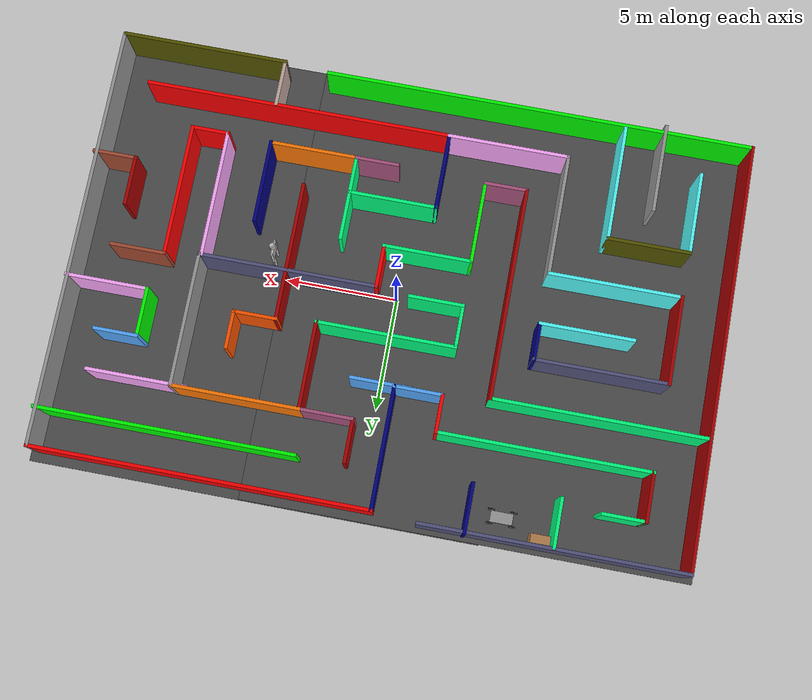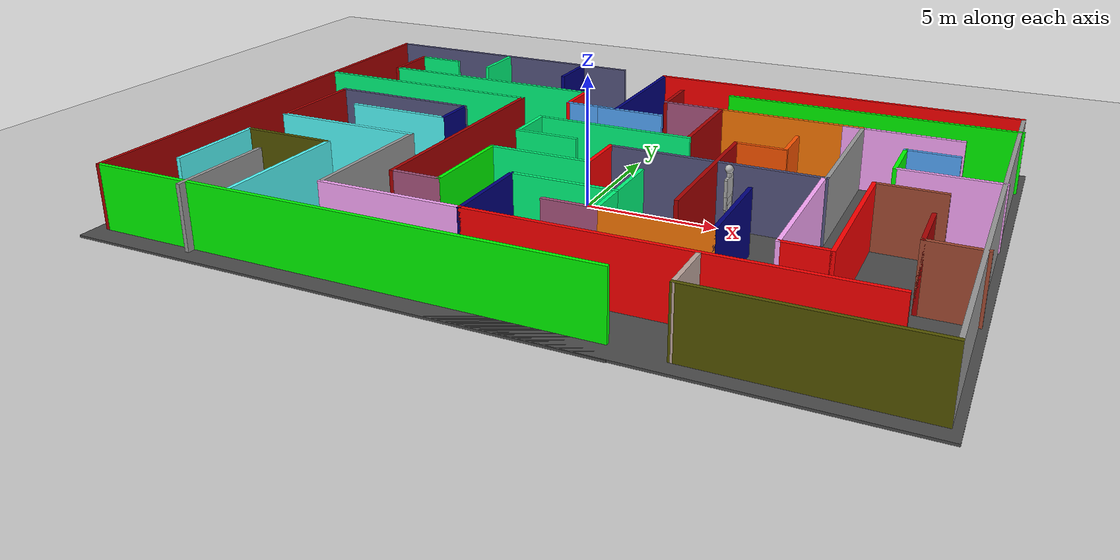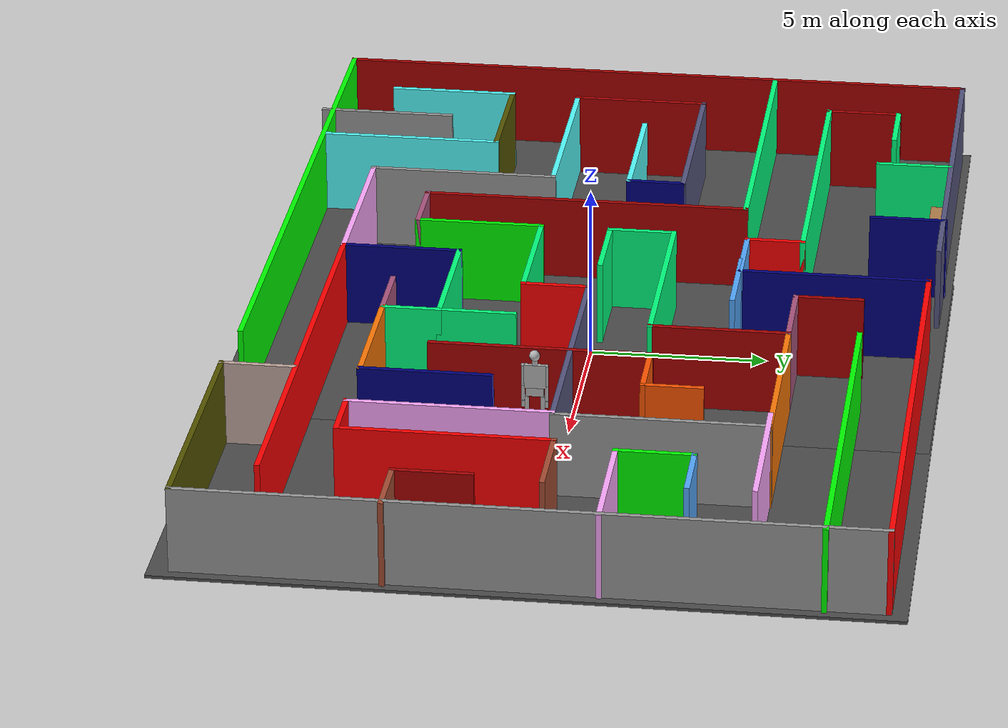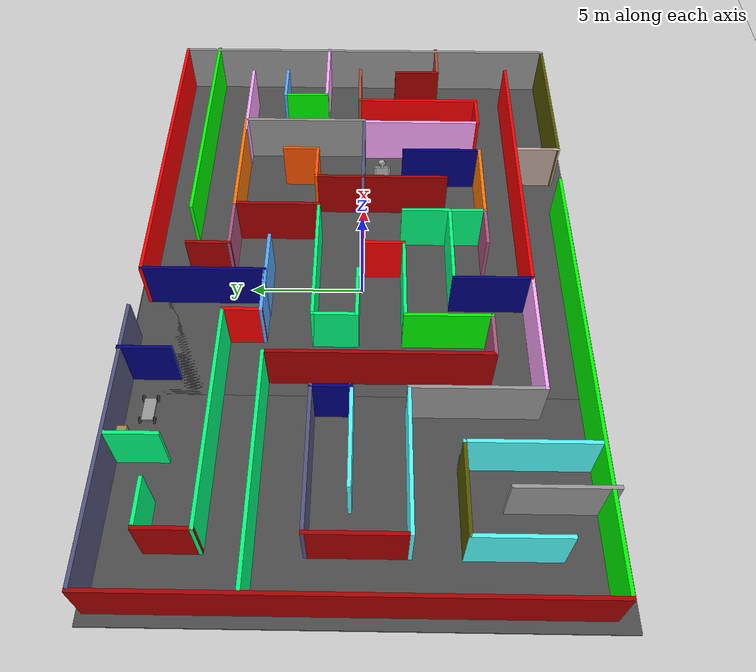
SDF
<sdf version="1.6">
 <world name="default">
  <light name="sun" type="directional">
   <pose>0 0 10 0 -0 0</pose>
   <diffuse>0.8 0.8 0.8 1</diffuse>
   <specular>0.1 0.1 0.1 1</specular>
   <attenuation>
    <range>1000</range>
    <constant>0.9</constant>
    <linear>0.01</linear>
    <quadratic>0.001</quadratic>
   </attenuation>
   <direction>-0.5 0.5 -1</direction>
  </light>
  <model name="ground_plane">
   <static>1</static>
   <link name="link">
    <collision name="collision">
     <geometry><plane><normal>0 0 1</normal><size>100 100</size></plane></geometry>
     <surface><friction><ode><mu>100</mu><mu2>50</mu2></ode></friction></surface>
    </collision>
    <visual name="visual">
     <cast_shadows>0</cast_shadows>
     <geometry><plane><normal>0 0 1</normal><size>100 100</size></plane></geometry>
     <material>
      <script><uri>file://media/materials/scripts/gazebo.material</uri><name>Gazebo/Grey</name></script>
     </material>
    </visual>
   </link>
  </model>
  <gravity>0 0 -9.8</gravity>
  <magnetic_field>6e-06 2.3e-05 -4.2e-05</magnetic_field>
  <atmosphere type="adiabatic"/>
  <physics name="default_physics" default="0" type="ode">
   <max_step_size>0.001</max_step_size>
   <real_time_factor>1</real_time_factor>
   <real_time_update_rate>1000</real_time_update_rate>
  </physics>
  <scene><ambient>0.4 0.4 0.4 1</ambient><background>0.7 0.7 0.7 1</background><shadows>1</shadows></scene>
  <spherical_coordinates>
   <surface_model>EARTH_WGS84</surface_model>
   <latitude_deg>0</latitude_deg>
   <longitude_deg>0</longitude_deg>
   <elevation>0</elevation>
   <heading_deg>0</heading_deg>
  </spherical_coordinates>
  <model name="medium_coloured_maze">
   <pose>-0.015602 0.148995 0 0 -0 0</pose>
   <link name="Wall_0">
    <collision name="Wall_0_Collision">
     <geometry><box><size>19 0.15 2.5</size></box></geometry>
     <pose>0 0 1.25 0 -0 0</pose>
    </collision>
    <visual name="Wall_0_Visual">
     <pose>0 0 1.25 0 -0 0</pose>
     <geometry><box><size>19 0.15 2.5</size></box></geometry>
     <material>
      <script><uri>file://media/materials/scripts/gazebo.material</uri><name>Gazebo/Grey</name></script>
      <ambient>0.666667 0 0 1</ambient>
     </material>
    </visual>
    <pose>-14.2862 0.111227 0 0 0 -1.5708</pose>
   </link>
   <link name="Wall_1">
    <collision name="Wall_1_Collision">
     <geometry><box><size>19.25 0.15 2.5</size></box></geometry>
     <pose>0 0 1.25 0 -0 0</pose>
    </collision>
    <visual name="Wall_1_Visual">
     <pose>0 0 1.25 0 -0 0</pose>
     <geometry><box><size>19.25 0.15 2.5</size></box></geometry>
     <material>
      <script><uri>file://media/materials/scripts/gazebo.material</uri><name>Gazebo/Grey</name></script>
      <ambient>0 1 0 1</ambient>
     </material>
    </visual>
    <pose>-4.73615 -9.31377 0 0 -0 0</pose>
   </link>
   <link name="Wall_10">
    <collision name="Wall_10_Collision">
     <geometry><box><size>2.25 0.15 2.5</size></box></geometry>
     <pose>0 0 1.25 0 -0 0</pose>
    </collision>
    <visual name="Wall_10_Visual">
     <pose>0 0 1.25 0 -0 0</pose>
     <geometry><box><size>2.25 0.15 2.5</size></box></geometry>
     <material>
      <script><uri>file://media/materials/scripts/gazebo.material</uri><name>Gazebo/Grey</name></script>
      <ambient>0.666667 0 0 1</ambient>
     </material>
    </visual>
    <pose>-12.1169 6.6789 0 0 -0 1.5708</pose>
   </link>
   <link name="Wall_11">
    <collision name="Wall_11_Collision">
     <geometry><box><size>2 0.15 2.5</size></box></geometry>
     <pose>0 0 1.25 0 -0 0</pose>
    </collision>
    <visual name="Wall_11_Visual">
     <pose>0 0 1.25 0 -0 0</pose>
     <geometry><box><size>2 0.15 2.5</size></box></geometry>
     <material>
      <script><uri>file://media/materials/scripts/gazebo.material</uri><name>Gazebo/Grey</name></script>
      <ambient>0 1 0.498039 1</ambient>
     </material>
    </visual>
    <pose>-11.1919 7.7289 0 0 -0 0</pose>
   </link>
   <link name="Wall_13">
    <collision name="Wall_13_Collision">
     <geometry><box><size>11.75 0.15 2.5</size></box></geometry>
     <pose>0 0 1.25 0 -0 0</pose>
    </collision>
    <visual name="Wall_13_Visual">
     <pose>0 0 1.25 0 -0 0</pose>
     <geometry><box><size>11.75 0.15 2.5</size></box></geometry>
     <material>
      <script><uri>file://media/materials/scripts/gazebo.material</uri><name>Gazebo/Grey</name></script>
      <ambient>0.333333 0.333333 0.498039 1</ambient>
     </material>
    </visual>
    <pose>-8.48615 9.53623 0 0 -0 0</pose>
   </link>
   <link name="Wall_15">
    <collision name="Wall_15_Collision">
     <geometry><box><size>2.25 0.15 2.5</size></box></geometry>
     <pose>0 0 1.25 0 -0 0</pose>
    </collision>
    <visual name="Wall_15_Visual">
     <pose>0 0 1.25 0 -0 0</pose>
     <geometry><box><size>2.25 0.15 2.5</size></box></geometry>
     <material>
      <script><uri>file://media/materials/scripts/gazebo.material</uri><name>Gazebo/Grey</name></script>
      <ambient>0 1 0.498039 1</ambient>
     </material>
    </visual>
    <pose>-8.47981 8.45384 0 0 0 -1.5708</pose>
   </link>
   <link name="Wall_18">
    <collision name="Wall_18_Collision">
     <geometry><box><size>2.25 0.15 2.5</size></box></geometry>
     <pose>0 0 1.25 0 -0 0</pose>
    </collision>
    <visual name="Wall_18_Visual">
     <pose>0 0 1.25 0 -0 0</pose>
     <geometry><box><size>2.25 0.15 2.5</size></box></geometry>
     <material>
      <script><uri>file://media/materials/scripts/gazebo.material</uri><name>Gazebo/Grey</name></script>
      <ambient>0 0 0.498039 1</ambient>
     </material>
    </visual>
    <pose>-4.69991 8.53531 0 0 0 -1.5708</pose>
   </link>
   <link name="Wall_20">
    <collision name="Wall_20_Collision">
     <geometry><box><size>9.5 0.15 2.5</size></box></geometry>
     <pose>0 0 1.25 0 -0 0</pose>
    </collision>
    <visual name="Wall_20_Visual">
     <pose>0 0 1.25 0 -0 0</pose>
     <geometry><box><size>9.5 0.15 2.5</size></box></geometry>
     <material>
      <script><uri>file://media/materials/scripts/gazebo.material</uri><name>Gazebo/Grey</name></script>
      <ambient>0 1 0.498039 1</ambient>
     </material>
    </visual>
    <pose>-9.46955 3.79078 0 0 -0 0</pose>
   </link>
   <link name="Wall_21">
    <collision name="Wall_21_Collision">
     <geometry><box><size>9.5 0.15 2.5</size></box></geometry>
     <pose>0 0 1.25 0 -0 0</pose>
    </collision>
    <visual name="Wall_21_Visual">
     <pose>0 0 1.25 0 -0 0</pose>
     <geometry><box><size>9.5 0.15 2.5</size></box></geometry>
     <material>
      <script><uri>file://media/materials/scripts/gazebo.material</uri><name>Gazebo/Grey</name></script>
      <ambient>0.666667 0 0 1</ambient>
     </material>
    </visual>
    <pose>-4.79455 -0.884224 0 0 0 -1.5708</pose>
   </link>
   <link name="Wall_22">
    <collision name="Wall_22_Collision">
     <geometry><box><size>2 0.15 2.5</size></box></geometry>
     <pose>0 0 1.25 0 -0 0</pose>
    </collision>
    <visual name="Wall_22_Visual">
     <pose>0 0 1.25 0 -0 0</pose>
     <geometry><box><size>2 0.15 2.5</size></box></geometry>
     <material>
      <script><uri>file://media/materials/scripts/gazebo.material</uri><name>Gazebo/Grey</name></script>
      <ambient>0.666667 0.333333 0.498039 1</ambient>
     </material>
    </visual>
    <pose>-3.86955 -5.55922 0 0 -0 0</pose>
   </link>
   <link name="Wall_23">
    <collision name="Wall_23_Collision">
     <geometry><box><size>3.75 0.15 2.5</size></box></geometry>
     <pose>0 0 1.25 0 -0 0</pose>
    </collision>
    <visual name="Wall_23_Visual">
     <pose>0 0 1.25 0 -0 0</pose>
     <geometry><box><size>3.75 0.15 2.5</size></box></geometry>
     <material>
      <script><uri>file://media/materials/scripts/gazebo.material</uri><name>Gazebo/Grey</name></script>
      <ambient>0 1 0 1</ambient>
     </material>
    </visual>
    <pose>-2.94455 -3.75922 0 0 -0 1.5708</pose>
   </link>
   <link name="Wall_24">
    <collision name="Wall_24_Collision">
     <geometry><box><size>4 0.15 2.5</size></box></geometry>
     <pose>0 0 1.25 0 -0 0</pose>
    </collision>
    <visual name="Wall_24_Visual">
     <pose>0 0 1.25 0 -0 0</pose>
     <geometry><box><size>4 0.15 2.5</size></box></geometry>
     <material>
      <script><uri>file://media/materials/scripts/gazebo.material</uri><name>Gazebo/Grey</name></script>
      <ambient>0 1 0.498039 1</ambient>
     </material>
    </visual>
    <pose>-1.01955 -1.95922 0 0 -0 0</pose>
   </link>
   <link name="Wall_25">
    <collision name="Wall_25_Collision">
     <geometry><box><size>2 0.15 2.5</size></box></geometry>
     <pose>0 0 1.25 0 -0 0</pose>
    </collision>
    <visual name="Wall_25_Visual">
     <pose>0 0 1.25 0 -0 0</pose>
     <geometry><box><size>2 0.15 2.5</size></box></geometry>
     <material>
      <script><uri>file://media/materials/scripts/gazebo.material</uri><name>Gazebo/Grey</name></script>
      <ambient>1 0 0 1</ambient>
     </material>
    </visual>
    <pose>0.905454 -1.03422 0 0 -0 1.5708</pose>
   </link>
   <link name="Wall_26">
    <collision name="Wall_26_Collision">
     <geometry><box><size>8 0.15 2.5</size></box></geometry>
     <pose>0 0 1.25 0 -0 0</pose>
    </collision>
    <visual name="Wall_26_Visual">
     <pose>0 0 1.25 0 -0 0</pose>
     <geometry><box><size>8 0.15 2.5</size></box></geometry>
     <material>
      <script><uri>file://media/materials/scripts/gazebo.material</uri><name>Gazebo/Grey</name></script>
      <ambient>0.333333 0.333333 0.498039 1</ambient>
     </material>
    </visual>
    <pose>4.83045 -0.109224 0 0 -0 0</pose>
   </link>
   <link name="Wall_27">
    <collision name="Wall_27_Collision">
     <geometry><box><size>6 0.15 2.5</size></box></geometry>
     <pose>0 0 1.25 0 -0 0</pose>
    </collision>
    <visual name="Wall_27_Visual">
     <pose>0 0 1.25 0 -0 0</pose>
     <geometry><box><size>6 0.15 2.5</size></box></geometry>
     <material>
      <script><uri>file://media/materials/scripts/gazebo.material</uri><name>Gazebo/Grey</name></script>
      <ambient>0 0 0 1</ambient>
     </material>
    </visual>
    <pose>8.75545 2.81578 0 0 -0 1.5708</pose>
   </link>
   <link name="Wall_28">
    <collision name="Wall_28_Collision">
     <geometry><box><size>5.75 0.15 2.5</size></box></geometry>
     <pose>0 0 1.25 0 -0 0</pose>
    </collision>
    <visual name="Wall_28_Visual">
     <pose>0 0 1.25 0 -0 0</pose>
     <geometry><box><size>5.75 0.15 2.5</size></box></geometry>
     <material>
      <script><uri>file://media/materials/scripts/gazebo.material</uri><name>Gazebo/Grey</name></script>
      <ambient>0.996078 0.47451 0.0196078 1</ambient>
     </material>
    </visual>
    <pose>5.95545 5.74078 0 0 -0 3.14159</pose>
   </link>
   <link name="Wall_29">
    <collision name="Wall_29_Collision">
     <geometry><box><size>4 0.15 2.5</size></box></geometry>
     <pose>0 0 1.25 0 -0 0</pose>
    </collision>
    <visual name="Wall_29_Visual">
     <pose>0 0 1.25 0 -0 0</pose>
     <geometry><box><size>4 0.15 2.5</size></box></geometry>
     <material>
      <script><uri>file://media/materials/scripts/gazebo.material</uri><name>Gazebo/Grey</name></script>
      <ambient>0.666667 0 0 1</ambient>
     </material>
    </visual>
    <pose>3.15545 3.81578 0 0 0 -1.5708</pose>
   </link>
   <link name="Wall_3">
    <collision name="Wall_3_Collision">
     <geometry><box><size>7.5 0.15 2.5</size></box></geometry>
     <pose>0 0 1.25 0 -0 0</pose>
    </collision>
    <visual name="Wall_3_Visual">
     <pose>0 0 1.25 0 -0 0</pose>
     <geometry><box><size>7.5 0.15 2.5</size></box></geometry>
     <material>
      <script><uri>file://media/materials/scripts/gazebo.material</uri><name>Gazebo/Grey</name></script>
      <ambient>0.333333 0.333333 0 1</ambient>
     </material>
    </visual>
    <pose>10.5081 -9.4711 0 0 -0 0</pose>
   </link>
   <link name="Wall_30">
    <collision name="Wall_30_Collision">
     <geometry><box><size>6.25 0.15 2.5</size></box></geometry>
     <pose>0 0 1.25 0 -0 0</pose>
    </collision>
    <visual name="Wall_30_Visual">
     <pose>0 0 1.25 0 -0 0</pose>
     <geometry><box><size>6.25 0.15 2.5</size></box></geometry>
     <material>
      <script><uri>file://media/materials/scripts/gazebo.material</uri><name>Gazebo/Grey</name></script>
      <ambient>0 1 0.498039 1</ambient>
     </material>
    </visual>
    <pose>0.105454 1.89078 0 0 -0 3.14159</pose>
   </link>
   <link name="Wall_31">
    <collision name="Wall_31_Collision">
     <geometry><box><size>2 0.15 2.5</size></box></geometry>
     <pose>0 0 1.25 0 -0 0</pose>
    </collision>
    <visual name="Wall_31_Visual">
     <pose>0 0 1.25 0 -0 0</pose>
     <geometry><box><size>2 0.15 2.5</size></box></geometry>
     <material>
      <script><uri>file://media/materials/scripts/gazebo.material</uri><name>Gazebo/Grey</name></script>
      <ambient>0 1 0.498039 1</ambient>
     </material>
    </visual>
    <pose>-2.94455 0.965776 0 0 0 -1.5708</pose>
   </link>
   <link name="Wall_32">
    <collision name="Wall_32_Collision">
     <geometry><box><size>2.5 0.15 2.5</size></box></geometry>
     <pose>0 0 1.25 0 -0 0</pose>
    </collision>
    <visual name="Wall_32_Visual">
     <pose>0 0 1.25 0 -0 0</pose>
     <geometry><box><size>2.5 0.15 2.5</size></box></geometry>
     <material>
      <script><uri>file://media/materials/scripts/gazebo.material</uri><name>Gazebo/Grey</name></script>
      <ambient>0 1 0.498039 1</ambient>
     </material>
    </visual>
    <pose>-1.76955 0.040776 0 0 -0 0</pose>
   </link>
   <link name="Wall_34">
    <collision name="Wall_34_Collision">
     <geometry><box><size>4.25 0.15 2.5</size></box></geometry>
     <pose>0 0 1.25 0 -0 0</pose>
    </collision>
    <visual name="Wall_34_Visual">
     <pose>0 0 1.25 0 -0 0</pose>
     <geometry><box><size>4.25 0.15 2.5</size></box></geometry>
     <material>
      <script><uri>file://media/materials/scripts/gazebo.material</uri><name>Gazebo/Grey</name></script>
      <ambient>0.333333 1 1 1</ambient>
     </material>
    </visual>
    <pose>-8.39882 0.186302 0 0 -0 0</pose>
   </link>
   <link name="Wall_35">
    <collision name="Wall_35_Collision">
     <geometry><box><size>1.75 0.15 2.5</size></box></geometry>
     <pose>0 0 1.25 0 -0 0</pose>
    </collision>
    <visual name="Wall_35_Visual">
     <pose>0 0 1.25 0 -0 0</pose>
     <geometry><box><size>1.75 0.15 2.5</size></box></geometry>
     <material>
      <script><uri>file://media/materials/scripts/gazebo.material</uri><name>Gazebo/Grey</name></script>
      <ambient>0 0 0.498039 1</ambient>
     </material>
    </visual>
    <pose>-6.34882 0.986302 0 0 -0 1.5708</pose>
   </link>
   <link name="Wall_36">
    <collision name="Wall_36_Collision">
     <geometry><box><size>6 0.15 2.5</size></box></geometry>
     <pose>0 0 1.25 0 -0 0</pose>
    </collision>
    <visual name="Wall_36_Visual">
     <pose>0 0 1.25 0 -0 0</pose>
     <geometry><box><size>6 0.15 2.5</size></box></geometry>
     <material>
      <script><uri>file://media/materials/scripts/gazebo.material</uri><name>Gazebo/Grey</name></script>
      <ambient>0.333333 0.333333 0.498039 1</ambient>
     </material>
    </visual>
    <pose>-9.27382 1.7863 0 0 -0 3.14159</pose>
   </link>
   <link name="Wall_37">
    <collision name="Wall_37_Collision">
     <geometry><box><size>4 0.15 2.5</size></box></geometry>
     <pose>0 0 1.25 0 -0 0</pose>
    </collision>
    <visual name="Wall_37_Visual">
     <pose>0 0 1.25 0 -0 0</pose>
     <geometry><box><size>4 0.15 2.5</size></box></geometry>
     <material>
      <script><uri>file://media/materials/scripts/gazebo.material</uri><name>Gazebo/Grey</name></script>
      <ambient>0.666667 0 0 1</ambient>
     </material>
    </visual>
    <pose>-12.1988 -0.138698 0 0 0 -1.5708</pose>
   </link>
   <link name="Wall_38">
    <collision name="Wall_38_Collision">
     <geometry><box><size>6 0.15 2.5</size></box></geometry>
     <pose>0 0 1.25 0 -0 0</pose>
    </collision>
    <visual name="Wall_38_Visual">
     <pose>0 0 1.25 0 -0 0</pose>
     <geometry><box><size>6 0.15 2.5</size></box></geometry>
     <material>
      <script><uri>file://media/materials/scripts/gazebo.material</uri><name>Gazebo/Grey</name></script>
      <ambient>0.333333 1 1 1</ambient>
     </material>
    </visual>
    <pose>-9.27382 -2.0637 0 0 -0 0</pose>
   </link>
   <link name="Wall_39">
    <collision name="Wall_39_Collision">
     <geometry><box><size>5.5 0.15 2.5</size></box></geometry>
     <pose>0 0 1.25 0 -0 0</pose>
    </collision>
    <visual name="Wall_39_Visual">
     <pose>0 0 1.25 0 -0 0</pose>
     <geometry><box><size>5.5 0.15 2.5</size></box></geometry>
     <material>
      <script><uri>file://media/materials/scripts/gazebo.material</uri><name>Gazebo/Grey</name></script>
      <ambient>0 0 0 1</ambient>
     </material>
    </visual>
    <pose>-6.34882 -4.7387 0 0 0 -1.5708</pose>
   </link>
   <link name="Wall_4">
    <collision name="Wall_4_Collision">
     <geometry><box><size>19 0.15 2.5</size></box></geometry>
     <pose>0 0 1.25 0 -0 0</pose>
    </collision>
    <visual name="Wall_4_Visual">
     <pose>0 0 1.25 0 -0 0</pose>
     <geometry><box><size>19 0.15 2.5</size></box></geometry>
     <material>
      <script><uri>file://media/materials/scripts/gazebo.material</uri><name>Gazebo/Grey</name></script>
      <ambient>0 0 0 1</ambient>
     </material>
    </visual>
    <pose>14.1831 -0.046098 0 0 -0 1.5708</pose>
   </link>
   <link name="Wall_40">
    <collision name="Wall_40_Collision">
     <geometry><box><size>5.5 0.15 2.5</size></box></geometry>
     <pose>0 0 1.25 0 -0 0</pose>
    </collision>
    <visual name="Wall_40_Visual">
     <pose>0 0 1.25 0 -0 0</pose>
     <geometry><box><size>5.5 0.15 2.5</size></box></geometry>
     <material>
      <script><uri>file://media/materials/scripts/gazebo.material</uri><name>Gazebo/Grey</name></script>
      <ambient>1 0.666667 1 1</ambient>
     </material>
    </visual>
    <pose>-3.67382 -7.4137 0 0 -0 0</pose>
   </link>
   <link name="Wall_41">
    <collision name="Wall_41_Collision">
     <geometry><box><size>3.5 0.15 2.5</size></box></geometry>
     <pose>0 0 1.25 0 -0 0</pose>
    </collision>
    <visual name="Wall_41_Visual">
     <pose>0 0 1.25 0 -0 0</pose>
     <geometry><box><size>3.5 0.15 2.5</size></box></geometry>
     <material>
      <script><uri>file://media/materials/scripts/gazebo.material</uri><name>Gazebo/Grey</name></script>
      <ambient>0 0 0.498039 1</ambient>
     </material>
    </visual>
    <pose>-0.99882 -5.7387 0 0 -0 1.5708</pose>
   </link>
   <link name="Wall_42">
    <collision name="Wall_42_Collision">
     <geometry><box><size>4 0.15 2.5</size></box></geometry>
     <pose>0 0 1.25 0 -0 0</pose>
    </collision>
    <visual name="Wall_42_Visual">
     <pose>0 0 1.25 0 -0 0</pose>
     <geometry><box><size>4 0.15 2.5</size></box></geometry>
     <material>
      <script><uri>file://media/materials/scripts/gazebo.material</uri><name>Gazebo/Grey</name></script>
      <ambient>0 1 0.498039 1</ambient>
     </material>
    </visual>
    <pose>0.92618 -4.0637 0 0 -0 0</pose>
   </link>
   <link name="Wall_43">
    <collision name="Wall_43_Collision">
     <geometry><box><size>1.75 0.15 2.5</size></box></geometry>
     <pose>0 0 1.25 0 -0 0</pose>
    </collision>
    <visual name="Wall_43_Visual">
     <pose>0 0 1.25 0 -0 0</pose>
     <geometry><box><size>1.75 0.15 2.5</size></box></geometry>
     <material>
      <script><uri>file://media/materials/scripts/gazebo.material</uri><name>Gazebo/Grey</name></script>
      <ambient>0 1 0.498039 1</ambient>
     </material>
    </visual>
    <pose>2.85118 -4.8637 0 0 0 -1.5708</pose>
   </link>
   <link name="Wall_44">
    <collision name="Wall_44_Collision">
     <geometry><box><size>4 0.15 2.5</size></box></geometry>
     <pose>0 0 1.25 0 -0 0</pose>
    </collision>
    <visual name="Wall_44_Visual">
     <pose>0 0 1.25 0 -0 0</pose>
     <geometry><box><size>4 0.15 2.5</size></box></geometry>
     <material>
      <script><uri>file://media/materials/scripts/gazebo.material</uri><name>Gazebo/Grey</name></script>
      <ambient>0.996078 0.47451 0.0196078 1</ambient>
     </material>
    </visual>
    <pose>4.77618 -5.6637 0 0 -0 0</pose>
   </link>
   <link name="Wall_45">
    <collision name="Wall_45_Collision">
     <geometry><box><size>3.75 0.15 2.5</size></box></geometry>
     <pose>0 0 1.25 0 -0 0</pose>
    </collision>
    <visual name="Wall_45_Visual">
     <pose>0 0 1.25 0 -0 0</pose>
     <geometry><box><size>3.75 0.15 2.5</size></box></geometry>
     <material>
      <script><uri>file://media/materials/scripts/gazebo.material</uri><name>Gazebo/Grey</name></script>
      <ambient>0 0 0.498039 1</ambient>
     </material>
    </visual>
    <pose>6.70118 -3.8637 0 0 -0 1.5708</pose>
   </link>
   <link name="Wall_47">
    <collision name="Wall_47_Collision">
     <geometry><box><size>1.75 0.15 2.5</size></box></geometry>
     <pose>0 0 1.25 0 -0 0</pose>
    </collision>
    <visual name="Wall_47_Visual">
     <pose>0 0 1.25 0 -0 0</pose>
     <geometry><box><size>1.75 0.15 2.5</size></box></geometry>
     <material>
      <script><uri>file://media/materials/scripts/gazebo.material</uri><name>Gazebo/Grey</name></script>
      <ambient>1 0.333333 0 1</ambient>
     </material>
    </visual>
    <pose>6.75228 2.89952 0 0 0 -1.5708</pose>
   </link>
   <link name="Wall_48">
    <collision name="Wall_48_Collision">
     <geometry><box><size>2 0.15 2.5</size></box></geometry>
     <pose>0 0 1.25 0 -0 0</pose>
    </collision>
    <visual name="Wall_48_Visual">
     <pose>0 0 1.25 0 -0 0</pose>
     <geometry><box><size>2 0.15 2.5</size></box></geometry>
     <material>
      <script><uri>file://media/materials/scripts/gazebo.material</uri><name>Gazebo/Grey</name></script>
      <ambient>1 0.333333 0 1</ambient>
     </material>
    </visual>
    <pose>5.82728 2.09952 0 0 -0 3.14159</pose>
   </link>
   <link name="Wall_49">
    <collision name="Wall_49_Collision">
     <geometry><box><size>6.25 0.15 2.5</size></box></geometry>
     <pose>0 0 1.25 0 -0 0</pose>
    </collision>
    <visual name="Wall_49_Visual">
     <pose>0 0 1.25 0 -0 0</pose>
     <geometry><box><size>6.25 0.15 2.5</size></box></geometry>
     <material>
      <script><uri>file://media/materials/scripts/gazebo.material</uri><name>Gazebo/Grey</name></script>
      <ambient>0.666667 0 0 1</ambient>
     </material>
    </visual>
    <pose>4.90228 -0.950477 0 0 0 -1.5708</pose>
   </link>
   <link name="Wall_5">
    <collision name="Wall_5_Collision">
     <geometry><box><size>15 0.15 2.5</size></box></geometry>
     <pose>0 0 1.25 0 -0 0</pose>
    </collision>
    <visual name="Wall_5_Visual">
     <pose>0 0 1.25 0 -0 0</pose>
     <geometry><box><size>15 0.15 2.5</size></box></geometry>
     <material>
      <script><uri>file://media/materials/scripts/gazebo.material</uri><name>Gazebo/Grey</name></script>
      <ambient>1 0 0 1</ambient>
     </material>
    </visual>
    <pose>6.7581 9.3789 0 0 -0 3.14159</pose>
   </link>
   <link name="Wall_51">
    <collision name="Wall_51_Collision">
     <geometry><box><size>2.25 0.15 2.5</size></box></geometry>
     <pose>0 0 1.25 0 -0 0</pose>
    </collision>
    <visual name="Wall_51_Visual">
     <pose>0 0 1.25 0 -0 0</pose>
     <geometry><box><size>2.25 0.15 2.5</size></box></geometry>
     <material>
      <script><uri>file://media/materials/scripts/gazebo.material</uri><name>Gazebo/Grey</name></script>
      <ambient>0 1 0.498039 1</ambient>
     </material>
    </visual>
    <pose>2.85118 -3.0137 0 0 -0 1.5708</pose>
   </link>
   <link name="Wall_53">
    <collision name="Wall_53_Collision">
     <geometry><box><size>2 0.15 2.5</size></box></geometry>
     <pose>0 0 1.25 0 -0 0</pose>
    </collision>
    <visual name="Wall_53_Visual">
     <pose>0 0 1.25 0 -0 0</pose>
     <geometry><box><size>2 0.15 2.5</size></box></geometry>
     <material>
      <script><uri>file://media/materials/scripts/gazebo.material</uri><name>Gazebo/Grey</name></script>
      <ambient>0.666667 0.333333 0.498039 1</ambient>
     </material>
    </visual>
    <pose>1.92618 -5.6637 0 0 -0 3.14159</pose>
   </link>
   <link name="Wall_56">
    <collision name="Wall_56_Collision">
     <geometry><box><size>13.75 0.15 2.5</size></box></geometry>
     <pose>0 0 1.25 0 -0 0</pose>
    </collision>
    <visual name="Wall_56_Visual">
     <pose>0 0 1.25 0 -0 0</pose>
     <geometry><box><size>13.75 0.15 2.5</size></box></geometry>
     <material>
      <script><uri>file://media/materials/scripts/gazebo.material</uri><name>Gazebo/Grey</name></script>
      <ambient>1 0 0 1</ambient>
     </material>
    </visual>
    <pose>5.80118 -7.4137 0 0 -0 0</pose>
   </link>
   <link name="Wall_58">
    <collision name="Wall_58_Collision">
     <geometry><box><size>2.16629 0.15 2.5</size></box></geometry>
     <pose>0 0 1.25 0 -0 0</pose>
    </collision>
    <visual name="Wall_58_Visual">
     <pose>0 0 1.25 0 -0 0</pose>
     <geometry><box><size>2.16629 0.15 2.5</size></box></geometry>
     <material>
      <script><uri>file://media/materials/scripts/gazebo.material</uri><name>Gazebo/Grey</name></script>
      <ambient>0.760784 0.662745 0.627451 1</ambient>
     </material>
    </visual>
    <pose>6.84013 -8.46298 0 0 0 -1.57777</pose>
   </link>
   <link name="Wall_6">
    <collision name="Wall_6_Collision">
     <geometry><box><size>5.5 0.15 2.5</size></box></geometry>
     <pose>0 0 1.25 0 -0 0</pose>
    </collision>
    <visual name="Wall_6_Visual">
     <pose>0 0 1.25 0 -0 0</pose>
     <geometry><box><size>5.5 0.15 2.5</size></box></geometry>
     <material>
      <script><uri>file://media/materials/scripts/gazebo.material</uri><name>Gazebo/Grey</name></script>
      <ambient>0 0 0.498039 1</ambient>
     </material>
    </visual>
    <pose>-0.666901 6.7039 0 0 0 -1.5708</pose>
   </link>
   <link name="Wall_60">
    <collision name="Wall_60_Collision">
     <geometry><box><size>2.5 0.15 2.5</size></box></geometry>
     <pose>0 0 1.25 0 -0 0</pose>
    </collision>
    <visual name="Wall_60_Visual">
     <pose>0 0 1.25 0 -0 0</pose>
     <geometry><box><size>2.5 0.15 2.5</size></box></geometry>
     <material>
      <script><uri>file://media/materials/scripts/gazebo.material</uri><name>Gazebo/Bricks</name></script>
      <ambient>1 1 1 1</ambient>
     </material>
    </visual>
    <pose>11.4337 0.135142 0 0 -0 3.14159</pose>
   </link>
   <link name="Wall_61">
    <collision name="Wall_61_Collision">
     <geometry><box><size>6 0.15 2.5</size></box></geometry>
     <pose>0 0 1.25 0 -0 0</pose>
    </collision>
    <visual name="Wall_61_Visual">
     <pose>0 0 1.25 0 -0 0</pose>
     <geometry><box><size>6 0.15 2.5</size></box></geometry>
     <material>
      <script><uri>file://media/materials/scripts/gazebo.material</uri><name>Gazebo/Grey</name></script>
      <ambient>1 0 0 1</ambient>
     </material>
    </visual>
    <pose>10.2587 -2.78986 0 0 0 -1.5708</pose>
   </link>
   <link name="Wall_62">
    <collision name="Wall_62_Collision">
     <geometry><box><size>1.75 0.15 2.5</size></box></geometry>
     <pose>0 0 1.25 0 -0 0</pose>
    </collision>
    <visual name="Wall_62_Visual">
     <pose>0 0 1.25 0 -0 0</pose>
     <geometry><box><size>1.75 0.15 2.5</size></box></geometry>
     <material>
      <script><uri>file://media/materials/scripts/gazebo.material</uri><name>Gazebo/Grey</name></script>
      <ambient>1 0 0 1</ambient>
     </material>
    </visual>
    <pose>9.45865 -5.71486 0 0 -0 3.14159</pose>
   </link>
   <link name="Wall_63">
    <collision name="Wall_63_Collision">
     <geometry><box><size>5.75 0.15 2.5</size></box></geometry>
     <pose>0 0 1.25 0 -0 0</pose>
    </collision>
    <visual name="Wall_63_Visual">
     <pose>0 0 1.25 0 -0 0</pose>
     <geometry><box><size>5.75 0.15 2.5</size></box></geometry>
     <material>
      <script><uri>file://media/materials/scripts/gazebo.material</uri><name>Gazebo/Grey</name></script>
      <ambient>1 0.666667 1 1</ambient>
     </material>
    </visual>
    <pose>8.65865 -2.91486 0 0 -0 1.5708</pose>
   </link>
   <link name="Wall_65">
    <collision name="Wall_65_Collision">
     <geometry><box><size>2.25 0.15 2.5</size></box></geometry>
     <pose>0 0 1.25 0 -0 0</pose>
    </collision>
    <visual name="Wall_65_Visual">
     <pose>0 0 1.25 0 -0 0</pose>
     <geometry><box><size>2.25 0.15 2.5</size></box></geometry>
     <material>
      <script><uri>file://media/materials/scripts/gazebo.material</uri><name>Gazebo/Grey</name></script>
      <ambient>0.666667 0 0 1</ambient>
     </material>
    </visual>
    <pose>12.4362 -2.81236 0 0 0 -1.5708</pose>
   </link>
   <link name="Wall_66">
    <collision name="Wall_66_Collision">
     <geometry><box><size>2 0.15 2.5</size></box></geometry>
     <pose>0 0 1.25 0 -0 0</pose>
    </collision>
    <visual name="Wall_66_Visual">
     <pose>0 0 1.25 0 -0 0</pose>
     <geometry><box><size>2 0.15 2.5</size></box></geometry>
     <material>
      <script><uri>file://media/materials/scripts/gazebo.material</uri><name>Gazebo/Bricks</name></script>
      <ambient>1 1 1 1</ambient>
     </material>
    </visual>
    <pose>13.3612 -3.86236 0 0 -0 0</pose>
   </link>
   <link name="Wall_68">
    <collision name="Wall_68_Collision">
     <geometry><box><size>11.5 0.15 2.5</size></box></geometry>
     <pose>0 0 1.25 0 -0 0</pose>
    </collision>
    <visual name="Wall_68_Visual">
     <pose>0 0 1.25 0 -0 0</pose>
     <geometry><box><size>11.5 0.15 2.5</size></box></geometry>
     <material>
      <script><uri>file://media/materials/scripts/gazebo.material</uri><name>Gazebo/Grey</name></script>
      <ambient>0 1 0 1</ambient>
     </material>
    </visual>
    <pose>8.60983 7.69706 0 0 -0 0</pose>
   </link>
   <link name="Wall_7">
    <collision name="Wall_7_Collision">
     <geometry><box><size>2.25 0.15 2.5</size></box></geometry>
     <pose>0 0 1.25 0 -0 0</pose>
    </collision>
    <visual name="Wall_7_Visual">
     <pose>0 0 1.25 0 -0 0</pose>
     <geometry><box><size>2.25 0.15 2.5</size></box></geometry>
     <material>
      <script><uri>file://media/materials/scripts/gazebo.material</uri><name>Gazebo/Grey</name></script>
      <ambient>0.333333 0.666667 1 1</ambient>
     </material>
    </visual>
    <pose>-1.7169 4.0289 0 0 -0 3.14159</pose>
   </link>
   <link name="Wall_70">
    <collision name="Wall_70_Collision">
     <geometry><box><size>2 0.15 2.5</size></box></geometry>
     <pose>0 0 1.25 0 -0 0</pose>
    </collision>
    <visual name="Wall_70_Visual">
     <pose>0 0 1.25 0 -0 0</pose>
     <geometry><box><size>2 0.15 2.5</size></box></geometry>
     <material>
      <script><uri>file://media/materials/scripts/gazebo.material</uri><name>Gazebo/Grey</name></script>
      <ambient>0.333333 0.666667 1 1</ambient>
     </material>
    </visual>
    <pose>11.5594 3.91921 0 0 -0 3.14159</pose>
   </link>
   <link name="Wall_71">
    <collision name="Wall_71_Collision">
     <geometry><box><size>2.25 0.15 2.5</size></box></geometry>
     <pose>0 0 1.25 0 -0 0</pose>
    </collision>
    <visual name="Wall_71_Visual">
     <pose>0 0 1.25 0 -0 0</pose>
     <geometry><box><size>2.25 0.15 2.5</size></box></geometry>
     <material>
      <script><uri>file://media/materials/scripts/gazebo.material</uri><name>Gazebo/Grey</name></script>
      <ambient>0 1 0 1</ambient>
     </material>
    </visual>
    <pose>10.6344 2.86921 0 0 0 -1.5708</pose>
   </link>
   <link name="Wall_72">
    <collision name="Wall_72_Collision">
     <geometry><box><size>3.75 0.15 2.5</size></box></geometry>
     <pose>0 0 1.25 0 -0 0</pose>
    </collision>
    <visual name="Wall_72_Visual">
     <pose>0 0 1.25 0 -0 0</pose>
     <geometry><box><size>3.75 0.15 2.5</size></box></geometry>
     <material>
      <script><uri>file://media/materials/scripts/gazebo.material</uri><name>Gazebo/Grey</name></script>
      <ambient>1 0.666667 1 1</ambient>
     </material>
    </visual>
    <pose>12.4344 1.81921 0 0 -0 0</pose>
   </link>
   <link name="Wall_74">
    <collision name="Wall_74_Collision">
     <geometry><box><size>3.75 0.15 2.5</size></box></geometry>
     <pose>0 0 1.25 0 -0 0</pose>
    </collision>
    <visual name="Wall_74_Visual">
     <pose>0 0 1.25 0 -0 0</pose>
     <geometry><box><size>3.75 0.15 2.5</size></box></geometry>
     <material>
      <script><uri>file://media/materials/scripts/gazebo.material</uri><name>Gazebo/Grey</name></script>
      <ambient>0.333333 1 1 1</ambient>
     </material>
    </visual>
    <pose>-12.2291 -5.87671 0 0 -0 1.5708</pose>
   </link>
   <link name="Wall_75">
    <collision name="Wall_75_Collision">
     <geometry><box><size>3.75 0.15 2.5</size></box></geometry>
     <pose>0 0 1.25 0 -0 0</pose>
    </collision>
    <visual name="Wall_75_Visual">
     <pose>0 0 1.25 0 -0 0</pose>
     <geometry><box><size>3.75 0.15 2.5</size></box></geometry>
     <material>
      <script><uri>file://media/materials/scripts/gazebo.material</uri><name>Gazebo/Grey</name></script>
      <ambient>0.333333 0.333333 0 1</ambient>
     </material>
    </visual>
    <pose>-10.4291 -4.07671 0 0 -0 0</pose>
   </link>
   <link name="Wall_76">
    <collision name="Wall_76_Collision">
     <geometry><box><size>5.25 0.15 2.5</size></box></geometry>
     <pose>0 0 1.25 0 -0 0</pose>
    </collision>
    <visual name="Wall_76_Visual">
     <pose>0 0 1.25 0 -0 0</pose>
     <geometry><box><size>5.25 0.15 2.5</size></box></geometry>
     <material>
      <script><uri>file://media/materials/scripts/gazebo.material</uri><name>Gazebo/Grey</name></script>
      <ambient>0.333333 1 1 1</ambient>
     </material>
    </visual>
    <pose>-8.62905 -6.62671 0 0 0 -1.5708</pose>
   </link>
   <link name="Wall_78">
    <collision name="Wall_78_Collision">
     <geometry><box><size>4 0.15 2.5</size></box></geometry>
     <pose>0 0 1.25 0 -0 0</pose>
    </collision>
    <visual name="Wall_78_Visual">
     <pose>0 0 1.25 0 -0 0</pose>
     <geometry><box><size>4 0.15 2.5</size></box></geometry>
     <material>
      <script><uri>file://media/materials/scripts/gazebo.material</uri><name>Gazebo/Grey</name></script>
      <ambient>0 0 0 1</ambient>
     </material>
    </visual>
    <pose>-10.3926 -7.66031 0 0 0 -1.5708</pose>
   </link>
   <link name="Wall_8">
    <collision name="Wall_8_Collision">
     <geometry><box><size>1.75 0.15 2.5</size></box></geometry>
     <pose>0 0 1.25 0 -0 0</pose>
    </collision>
    <visual name="Wall_8_Visual">
     <pose>0 0 1.25 0 -0 0</pose>
     <geometry><box><size>1.75 0.15 2.5</size></box></geometry>
     <material>
      <script><uri>file://media/materials/scripts/gazebo.material</uri><name>Gazebo/Grey</name></script>
      <ambient>1 0 0 1</ambient>
     </material>
    </visual>
    <pose>-2.7669 4.8289 0 0 -0 1.5708</pose>
   </link>
   <link name="Wall_80">
    <collision name="Wall_80_Collision">
     <geometry><box><size>4.5 0.15 2.5</size></box></geometry>
     <pose>0 0 1.25 0 -0 0</pose>
    </collision>
    <visual name="Wall_80_Visual">
     <pose>0 0 1.25 0 -0 0</pose>
     <geometry><box><size>4.5 0.15 2.5</size></box></geometry>
     <material>
      <script><uri>file://media/materials/scripts/gazebo.material</uri><name>Gazebo/Grey</name></script>
      <ambient>1 0.666667 1 1</ambient>
     </material>
    </visual>
    <pose>10.2519 5.70319 0 0 -0 0</pose>
   </link>
   <link name="Wall_84">
    <collision name="Wall_84_Collision">
     <geometry><box><size>2.75 0.15 2.5</size></box></geometry>
     <pose>0 0 1.25 0 -0 0</pose>
    </collision>
    <visual name="Wall_84_Visual">
     <pose>0 0 1.25 0 -0 0</pose>
     <geometry><box><size>2.75 0.15 2.5</size></box></geometry>
     <material>
      <script><uri>file://media/materials/scripts/gazebo.material</uri><name>Gazebo/Grey</name></script>
      <ambient>0.333333 0.666667 1 1</ambient>
     </material>
    </visual>
    <pose>-0.070687 3.99264 0 0 -0 0</pose>
   </link>
   <link name="Wall_86">
    <collision name="Wall_86_Collision">
     <geometry><box><size>2.5 0.15 2.5</size></box></geometry>
     <pose>0 0 1.25 0 -0 0</pose>
    </collision>
    <visual name="Wall_86_Visual">
     <pose>0 0 1.25 0 -0 0</pose>
     <geometry><box><size>2.5 0.15 2.5</size></box></geometry>
     <material>
      <script><uri>file://media/materials/scripts/gazebo.material</uri><name>Gazebo/Grey</name></script>
      <ambient>0.666667 0.333333 0.498039 1</ambient>
     </material>
    </visual>
    <pose>1.98045 5.74078 0 0 -0 3.14159</pose>
   </link>
   <link name="Wall_87">
    <collision name="Wall_87_Collision">
     <geometry><box><size>2 0.15 2.5</size></box></geometry>
     <pose>0 0 1.25 0 -0 0</pose>
    </collision>
    <visual name="Wall_87_Visual">
     <pose>0 0 1.25 0 -0 0</pose>
     <geometry><box><size>2 0.15 2.5</size></box></geometry>
     <material>
      <script><uri>file://media/materials/scripts/gazebo.material</uri><name>Gazebo/Grey</name></script>
      <ambient>0.666667 0 0 1</ambient>
     </material>
    </visual>
    <pose>0.805454 6.66578 0 0 -0 1.5708</pose>
   </link>
   <link name="Wall_9">
    <collision name="Wall_9_Collision">
     <geometry><box><size>9.5 0.15 2.5</size></box></geometry>
     <pose>0 0 1.25 0 -0 0</pose>
    </collision>
    <visual name="Wall_9_Visual">
     <pose>0 0 1.25 0 -0 0</pose>
     <geometry><box><size>9.5 0.15 2.5</size></box></geometry>
     <material>
      <script><uri>file://media/materials/scripts/gazebo.material</uri><name>Gazebo/Grey</name></script>
      <ambient>0 1 0.498039 1</ambient>
     </material>
    </visual>
    <pose>-7.4419 5.6289 0 0 -0 3.14159</pose>
   </link>
   <static>1</static>
  </model>
  <model name="bookshelf">
   <static>1</static>
   <link name="link">
    <inertial><mass>1</mass></inertial>
    <collision name="back">
     <pose>0 0.005 0.6 0 -0 0</pose>
     <geometry><box><size>0.9 0.01 1.2</size></box></geometry>
    </collision>
    <visual name="visual1">
     <pose>0 0.005 0.6 0 -0 0</pose>
     <geometry><box><size>0.9 0.01 1.2</size></box></geometry>
     <material>
      <script><uri>file://media/materials/scripts/gazebo.material</uri><name>Gazebo/Wood</name></script>
     </material>
    </visual>
    <collision name="left_side">
     <pose>0.45 -0.195 0.6 0 -0 0</pose>
     <geometry><box><size>0.02 0.4 1.2</size></box></geometry>
    </collision>
    <visual name="visual2">
     <pose>0.45 -0.195 0.6 0 -0 0</pose>
     <geometry><box><size>0.02 0.4 1.2</size></box></geometry>
     <material>
      <script><uri>file://media/materials/scripts/gazebo.material</uri><name>Gazebo/Wood</name></script>
     </material>
    </visual>
    <collision name="right_side">
     <pose>-0.45 -0.195 0.6 0 -0 0</pose>
     <geometry><box><size>0.02 0.4 1.2</size></box></geometry>
    </collision>
    <visual name="visual3">
     <pose>-0.45 -0.195 0.6 0 -0 0</pose>
     <geometry><box><size>0.02 0.4 1.2</size></box></geometry>
     <material>
      <script><uri>file://media/materials/scripts/gazebo.material</uri><name>Gazebo/Wood</name></script>
     </material>
    </visual>
    <collision name="bottom">
     <pose>0 -0.195 0.03 0 -0 0</pose>
     <geometry><box><size>0.88 0.4 0.06</size></box></geometry>
    </collision>
    <visual name="visual4">
     <pose>0 -0.195 0.03 0 -0 0</pose>
     <geometry><box><size>0.88 0.4 0.06</size></box></geometry>
     <material>
      <script><uri>file://media/materials/scripts/gazebo.material</uri><name>Gazebo/Wood</name></script>
     </material>
    </visual>
    <collision name="top">
     <pose>0 -0.195 1.19 0 -0 0</pose>
     <geometry><box><size>0.88 0.4 0.02</size></box></geometry>
    </collision>
    <visual name="visual5">
     <pose>0 -0.195 1.19 0 -0 0</pose>
     <geometry><box><size>0.88 0.4 0.02</size></box></geometry>
     <material>
      <script><uri>file://media/materials/scripts/gazebo.material</uri><name>Gazebo/Wood</name></script>
     </material>
    </visual>
    <collision name="low_shelf">
     <pose>0 -0.195 0.43 0 -0 0</pose>
     <geometry><box><size>0.88 0.4 0.02</size></box></geometry>
    </collision>
    <visual name="visual6">
     <pose>0 -0.195 0.43 0 -0 0</pose>
     <geometry><box><size>0.88 0.4 0.02</size></box></geometry>
     <material>
      <script><uri>file://media/materials/scripts/gazebo.material</uri><name>Gazebo/Wood</name></script>
     </material>
    </visual>
    <collision name="high_shelf">
     <pose>0 -0.195 0.8 0 -0 0</pose>
     <geometry><box><size>0.88 0.4 0.02</size></box></geometry>
    </collision>
    <visual name="visual7">
     <pose>0 -0.195 0.8 0 -0 0</pose>
     <geometry><box><size>0.88 0.4 0.02</size></box></geometry>
     <material>
      <script><uri>file://media/materials/scripts/gazebo.material</uri><name>Gazebo/Wood</name></script>
     </material>
    </visual>
   </link>
   <pose>-7.98935 9.53232 0 0 -0 0</pose>
  </model>
  <model name="asphalt_plane">
   <static>1</static>
   <link name="link">
    <collision name="collision"><geometry><box><size>20 20 0.1</size></box></geometry></collision>
    <visual name="visual">
     <cast_shadows>0</cast_shadows>
     <geometry><box><size>20 20 0.1</size></box></geometry>
     <material>
      <script>
       <uri>model://asphalt_plane/materials/scripts</uri>
       <uri>model://asphalt_plane/materials/textures</uri>
       <name>vrc/asphalt</name>
      </script>
     </material>
    </visual>
   </link>
   <pose>4.52241 0.024318 0 0 -0 0</pose>
  </model>
  <model name="asphalt_plane_0">
   <static>1</static>
   <link name="link">
    <collision name="collision"><geometry><box><size>20 20 0.1</size></box></geometry></collision>
    <visual name="visual">
     <cast_shadows>0</cast_shadows>
     <geometry><box><size>20 20 0.1</size></box></geometry>
     <material>
      <script>
       <uri>model://asphalt_plane/materials/scripts</uri>
       <uri>model://asphalt_plane/materials/textures</uri>
       <name>vrc/asphalt</name>
      </script>
     </material>
    </visual>
   </link>
   <pose>-4.82142 -0.012158 0 0 -0 0</pose>
  </model>
  <model name="cart_front_steer">
   <link name="chassis">
    <pose>0 0 0.15 0 -0 0</pose>
    <inertial>
     <pose>0.1 0 0 0 -0 0</pose>
     <mass>10</mass>
     <inertia>
      <ixx>0.216667</ixx>
      <iyy>0.841667</iyy>
      <izz>1.04167</izz>
      <ixy>0</ixy>
      <ixz>0</ixz>
      <iyz>0</iyz>
     </inertia>
    </inertial>
    <collision name="collision"><geometry><box><size>1 0.5 0.1</size></box></geometry></collision>
    <visual name="visual">
     <geometry><box><size>1 0.5 0.1</size></box></geometry>
     <material>
      <script><uri>file://media/materials/scripts/gazebo.material</uri><name>Gazebo/Grey</name></script>
     </material>
    </visual>
   </link>
   <link name="wheel_front_left">
    <pose>0.5 0.298 0.15 -1.5708 -0.087266 0</pose>
    <inertial>
     <mass>0.5</mass>
     <inertia>
      <ixx>0.00307917</ixx>
      <iyy>0.00307917</iyy>
      <izz>0.005625</izz>
      <ixy>0</ixy>
      <ixz>0</ixz>
      <iyz>0</iyz>
     </inertia>
    </inertial>
    <collision name="collision">
     <geometry><cylinder><radius>0.15</radius><length>0.08</length></cylinder></geometry>
    </collision>
    <visual name="visual">
     <geometry><cylinder><radius>0.15</radius><length>0.08</length></cylinder></geometry>
     <material>
      <script><uri>file://media/materials/scripts/gazebo.material</uri><name>Gazebo/Black</name></script>
     </material>
    </visual>
   </link>
   <joint name="wheel_front_left_steer_spin" type="universal">
    <parent>chassis</parent>
    <child>wheel_front_left</child>
    <axis>
     <xyz>0 -1 0</xyz>
     <limit><lower>-0.610865</lower><upper>0.610865</upper></limit>
     <use_parent_model_frame>0</use_parent_model_frame>
     <dynamics><spring_reference>0</spring_reference><spring_stiffness>0</spring_stiffness></dynamics>
    </axis>
    <axis2>
     <xyz>0 0 1</xyz>
     <use_parent_model_frame>0</use_parent_model_frame>
     <dynamics><spring_reference>0</spring_reference><spring_stiffness>0</spring_stiffness></dynamics>
    </axis2>
   </joint>
   <link name="wheel_front_right">
    <pose>0.5 -0.298 0.15 -1.5708 -0.087266 0</pose>
    <inertial>
     <mass>0.5</mass>
     <inertia>
      <ixx>0.00307917</ixx>
      <iyy>0.00307917</iyy>
      <izz>0.005625</izz>
      <ixy>0</ixy>
      <ixz>0</ixz>
      <iyz>0</iyz>
     </inertia>
    </inertial>
    <collision name="collision">
     <geometry><cylinder><radius>0.15</radius><length>0.08</length></cylinder></geometry>
    </collision>
    <visual name="visual">
     <geometry><cylinder><radius>0.15</radius><length>0.08</length></cylinder></geometry>
     <material>
      <script><uri>file://media/materials/scripts/gazebo.material</uri><name>Gazebo/Black</name></script>
     </material>
    </visual>
   </link>
   <joint name="wheel_front_right_steer_spin" type="universal">
    <parent>chassis</parent>
    <child>wheel_front_right</child>
    <axis>
     <xyz>0 -1 0</xyz>
     <limit><lower>-0.610865</lower><upper>0.610865</upper></limit>
     <use_parent_model_frame>0</use_parent_model_frame>
     <dynamics><spring_reference>0</spring_reference><spring_stiffness>0</spring_stiffness></dynamics>
    </axis>
    <axis2>
     <xyz>0 0 1</xyz>
     <use_parent_model_frame>0</use_parent_model_frame>
     <dynamics><spring_reference>0</spring_reference><spring_stiffness>0</spring_stiffness></dynamics>
    </axis2>
   </joint>
   <link name="wheel_rear_left">
    <pose>-0.5 0.298 0.15 -1.5708 0 0</pose>
    <inertial>
     <mass>0.5</mass>
     <inertia>
      <ixx>0.00307917</ixx>
      <iyy>0.00307917</iyy>
      <izz>0.005625</izz>
      <ixy>0</ixy>
      <ixz>0</ixz>
      <iyz>0</iyz>
     </inertia>
    </inertial>
    <collision name="collision">
     <geometry><cylinder><radius>0.15</radius><length>0.08</length></cylinder></geometry>
    </collision>
    <visual name="visual">
     <geometry><cylinder><radius>0.15</radius><length>0.08</length></cylinder></geometry>
     <material>
      <script><uri>file://media/materials/scripts/gazebo.material</uri><name>Gazebo/Black</name></script>
     </material>
    </visual>
   </link>
   <joint name="wheel_rear_left_spin" type="revolute">
    <parent>chassis</parent>
    <child>wheel_rear_left</child>
    <axis>
     <xyz>0 0 1</xyz>
     <use_parent_model_frame>0</use_parent_model_frame>
     <limit><lower>-1e+16</lower><upper>1e+16</upper></limit>
     <dynamics><spring_reference>0</spring_reference><spring_stiffness>0</spring_stiffness></dynamics>
    </axis>
   </joint>
   <link name="wheel_rear_right">
    <pose>-0.5 -0.298 0.15 -1.5708 0 0</pose>
    <inertial>
     <mass>0.5</mass>
     <inertia>
      <ixx>0.00307917</ixx>
      <iyy>0.00307917</iyy>
      <izz>0.005625</izz>
      <ixy>0</ixy>
      <ixz>0</ixz>
      <iyz>0</iyz>
     </inertia>
    </inertial>
    <collision name="collision">
     <geometry><cylinder><radius>0.15</radius><length>0.08</length></cylinder></geometry>
    </collision>
    <visual name="visual">
     <geometry><cylinder><radius>0.15</radius><length>0.08</length></cylinder></geometry>
     <material>
      <script><uri>file://media/materials/scripts/gazebo.material</uri><name>Gazebo/Black</name></script>
     </material>
    </visual>
   </link>
   <joint name="wheel_rear_right_spin" type="revolute">
    <parent>chassis</parent>
    <child>wheel_rear_right</child>
    <axis>
     <xyz>0 0 1</xyz>
     <use_parent_model_frame>0</use_parent_model_frame>
     <limit><lower>-1e+16</lower><upper>1e+16</upper></limit>
     <dynamics><spring_reference>0</spring_reference><spring_stiffness>0</spring_stiffness></dynamics>
    </axis>
   </joint>
   <pose>-6.25992 8.68123 0 0 -0 0</pose>
  </model>
  <model name="ragdoll">
   <pose>5.64125 -0.843011 1.4 0 -0 0</pose>
   <link name="hip">
    <inertial>
     <inertia><ixx>0.1</ixx><ixy>0</ixy><ixz>0</ixz><iyy>0.1</iyy><iyz>0</iyz><izz>0.1</izz></inertia>
     <mass>10</mass>
    </inertial>
    <collision name="hip_geom">
     <pose>0 0 0.125 0 -0 0</pose>
     <geometry><box><size>0.1 0.5 0.25</size></box></geometry>
     <surface>
      <friction><ode><mu>-1</mu><mu2>-1</mu2><fdir1>0 0 0</fdir1><slip1>0</slip1><slip2>0</slip2></ode></friction>
      <bounce><restitution_coefficient>0</restitution_coefficient><threshold>100000</threshold></bounce>
      <contact>
       <ode>
        <soft_cfm>0</soft_cfm>
        <soft_erp>0.2</soft_erp>
        <kp>1e+12</kp>
        <kd>1</kd>
        <max_vel>0</max_vel>
        <min_depth>0.001</min_depth>
       </ode>
      </contact>
     </surface>
    </collision>
    <visual name="hip_geom_visual">
     <pose>0 0 0.125 0 -0 0</pose>
     <geometry><box><size>0.1 0.5 0.25</size></box></geometry>
    </visual>
    <gravity>0</gravity>
   </link>
   <link name="l_thigh_pan">
    <pose>0 0.22 0 0 -0 0</pose>
    <inertial>
     <inertia><ixx>0.01</ixx><ixy>0</ixy><ixz>0</ixz><iyy>0.01</iyy><iyz>0</iyz><izz>0.01</izz></inertia>
     <mass>1</mass>
    </inertial>
    <collision name="l_thigh_pan_geom">
     <pose>0 0 -0.03 0 -0 0</pose>
     <geometry><sphere><radius>0.06</radius></sphere></geometry>
     <surface>
      <friction><ode><mu>-1</mu><mu2>-1</mu2><fdir1>0 0 0</fdir1><slip1>0</slip1><slip2>0</slip2></ode></friction>
      <bounce><restitution_coefficient>0</restitution_coefficient><threshold>100000</threshold></bounce>
      <contact>
       <ode>
        <soft_cfm>0</soft_cfm>
        <soft_erp>0.2</soft_erp>
        <kp>1e+12</kp>
        <kd>1</kd>
        <max_vel>0</max_vel>
        <min_depth>0.001</min_depth>
       </ode>
      </contact>
     </surface>
    </collision>
    <visual name="l_thigh_pan_geom_visual">
     <pose>0 0 -0.03 0 -0 0</pose>
     <geometry><sphere><radius>0.06</radius></sphere></geometry>
    </visual>
    <gravity>0</gravity>
   </link>
   <link name="l_thigh_lift">
    <pose>0 0.22 0 0 -0 0</pose>
    <inertial>
     <inertia><ixx>0.05</ixx><ixy>0</ixy><ixz>0</ixz><iyy>0.05</iyy><iyz>0</iyz><izz>0.05</izz></inertia>
     <mass>5</mass>
    </inertial>
    <collision name="l_thigh_lift_geom">
     <pose>0 0 -0.35 0 -0 0</pose>
     <geometry><cylinder><radius>0.06</radius><length>0.7</length></cylinder></geometry>
     <surface>
      <friction><ode><mu>-1</mu><mu2>-1</mu2><fdir1>0 0 0</fdir1><slip1>0</slip1><slip2>0</slip2></ode></friction>
      <bounce><restitution_coefficient>0</restitution_coefficient><threshold>100000</threshold></bounce>
      <contact>
       <ode>
        <soft_cfm>0</soft_cfm>
        <soft_erp>0.2</soft_erp>
        <kp>1e+12</kp>
        <kd>1</kd>
        <max_vel>0</max_vel>
        <min_depth>0.001</min_depth>
       </ode>
      </contact>
     </surface>
    </collision>
    <visual name="l_thigh_lift_geom_visual">
     <pose>0 0 -0.35 0 -0 0</pose>
     <geometry><cylinder><radius>0.06</radius><length>0.7</length></cylinder></geometry>
    </visual>
    <gravity>0</gravity>
   </link>
   <link name="l_calf">
    <pose>0 0.22 -0.7 0 -0 0</pose>
    <inertial>
     <inertia><ixx>0.02</ixx><ixy>0</ixy><ixz>0</ixz><iyy>0.02</iyy><iyz>0</iyz><izz>0.02</izz></inertia>
     <mass>2</mass>
    </inertial>
    <collision name="l_calf_geom">
     <pose>0 0 -0.3 0 -0 0</pose>
     <geometry><cylinder><radius>0.05</radius><length>0.6</length></cylinder></geometry>
     <surface>
      <friction><ode><mu>-1</mu><mu2>-1</mu2><fdir1>0 0 0</fdir1><slip1>0</slip1><slip2>0</slip2></ode></friction>
      <bounce><restitution_coefficient>0</restitution_coefficient><threshold>100000</threshold></bounce>
      <contact>
       <ode>
        <soft_cfm>0</soft_cfm>
        <soft_erp>0.2</soft_erp>
        <kp>1e+12</kp>
        <kd>1</kd>
        <max_vel>0</max_vel>
        <min_depth>0.001</min_depth>
       </ode>
      </contact>
     </surface>
    </collision>
    <visual name="l_calf_geom_visual">
     <pose>0 0 -0.3 0 -0 0</pose>
     <geometry><cylinder><radius>0.05</radius><length>0.6</length></cylinder></geometry>
    </visual>
    <gravity>0</gravity>
   </link>
   <link name="l_ankle">
    <pose>0 0.22 -1.325 0 -0 0</pose>
    <inertial>
     <inertia><ixx>0.01</ixx><ixy>0</ixy><ixz>0</ixz><iyy>0.01</iyy><iyz>0</iyz><izz>0.01</izz></inertia>
     <mass>1</mass>
    </inertial>
    <collision name="l_ankle_geom">
     <geometry><sphere><radius>0.05</radius></sphere></geometry>
     <surface>
      <friction><ode><mu>-1</mu><mu2>-1</mu2><fdir1>0 0 0</fdir1><slip1>0</slip1><slip2>0</slip2></ode></friction>
      <bounce><restitution_coefficient>0</restitution_coefficient><threshold>100000</threshold></bounce>
      <contact>
       <ode>
        <soft_cfm>0</soft_cfm>
        <soft_erp>0.2</soft_erp>
        <kp>1e+12</kp>
        <kd>1</kd>
        <max_vel>0</max_vel>
        <min_depth>0.001</min_depth>
       </ode>
      </contact>
     </surface>
    </collision>
    <visual name="l_ankle_geom_visual"><geometry><sphere><radius>0.05</radius></sphere></geometry></visual>
    <gravity>0</gravity>
   </link>
   <link name="l_foot">
    <pose>0 0.22 -1.35 0 -0 0</pose>
    <inertial>
     <pose>0.1 0 0 0 -0 0</pose>
     <inertia><ixx>0.01</ixx><ixy>0</ixy><ixz>0</ixz><iyy>0.01</iyy><iyz>0</iyz><izz>0.01</izz></inertia>
     <mass>1</mass>
    </inertial>
    <collision name="l_foot_geom">
     <pose>0.1 0 -0.025 0 -0 0</pose>
     <geometry><box><size>0.2 0.03 0.05</size></box></geometry>
     <surface>
      <friction><ode><mu>-1</mu><mu2>-1</mu2><fdir1>0 0 0</fdir1><slip1>0</slip1><slip2>0</slip2></ode></friction>
      <bounce><restitution_coefficient>0</restitution_coefficient><threshold>100000</threshold></bounce>
      <contact>
       <ode>
        <soft_cfm>0</soft_cfm>
        <soft_erp>0.2</soft_erp>
        <kp>1e+12</kp>
        <kd>1</kd>
        <max_vel>0</max_vel>
        <min_depth>0.001</min_depth>
       </ode>
      </contact>
     </surface>
    </collision>
    <visual name="l_foot_geom_visual">
     <pose>0.1 0 -0.025 0 -0 0</pose>
     <geometry><box><size>0.2 0.03 0.05</size></box></geometry>
    </visual>
   </link>
   <link name="r_thigh_pan">
    <pose>0 -0.22 0 0 -0 0</pose>
    <inertial>
     <inertia><ixx>0.01</ixx><ixy>0</ixy><ixz>0</ixz><iyy>0.01</iyy><iyz>0</iyz><izz>0.01</izz></inertia>
     <mass>1</mass>
    </inertial>
    <collision name="r_thigh_pan_geom">
     <pose>0 0 -0.03 0 -0 0</pose>
     <geometry><sphere><radius>0.06</radius></sphere></geometry>
     <surface>
      <friction><ode><mu>-1</mu><mu2>-1</mu2><fdir1>0 0 0</fdir1><slip1>0</slip1><slip2>0</slip2></ode></friction>
      <bounce><restitution_coefficient>0</restitution_coefficient><threshold>100000</threshold></bounce>
      <contact>
       <ode>
        <soft_cfm>0</soft_cfm>
        <soft_erp>0.2</soft_erp>
        <kp>1e+12</kp>
        <kd>1</kd>
        <max_vel>0</max_vel>
        <min_depth>0.001</min_depth>
       </ode>
      </contact>
     </surface>
    </collision>
    <visual name="r_thigh_pan_geom_visual">
     <pose>0 0 -0.03 0 -0 0</pose>
     <geometry><sphere><radius>0.06</radius></sphere></geometry>
    </visual>
    <gravity>0</gravity>
   </link>
   <link name="r_thigh_lift">
    <pose>0 -0.22 0 0 -0 0</pose>
    <inertial>
     <inertia><ixx>0.05</ixx><ixy>0</ixy><ixz>0</ixz><iyy>0.05</iyy><iyz>0</iyz><izz>0.05</izz></inertia>
     <mass>5</mass>
    </inertial>
    <collision name="r_thigh_lift_geom">
     <pose>0 0 -0.35 0 -0 0</pose>
     <geometry><cylinder><radius>0.06</radius><length>0.7</length></cylinder></geometry>
     <surface>
      <friction><ode><mu>-1</mu><mu2>-1</mu2><fdir1>0 0 0</fdir1><slip1>0</slip1><slip2>0</slip2></ode></friction>
      <bounce><restitution_coefficient>0</restitution_coefficient><threshold>100000</threshold></bounce>
      <contact>
       <ode>
        <soft_cfm>0</soft_cfm>
        <soft_erp>0.2</soft_erp>
        <kp>1e+12</kp>
        <kd>1</kd>
        <max_vel>0</max_vel>
        <min_depth>0.001</min_depth>
       </ode>
      </contact>
     </surface>
    </collision>
    <visual name="r_thigh_lift_geom_visual">
     <pose>0 0 -0.35 0 -0 0</pose>
     <geometry><cylinder><radius>0.06</radius><length>0.7</length></cylinder></geometry>
    </visual>
    <gravity>0</gravity>
   </link>
   <link name="r_calf">
    <pose>0 -0.22 -0.7 0 -0 0</pose>
    <inertial>
     <inertia><ixx>0.02</ixx><ixy>0</ixy><ixz>0</ixz><iyy>0.02</iyy><iyz>0</iyz><izz>0.02</izz></inertia>
     <mass>2</mass>
    </inertial>
    <collision name="r_calf_geom">
     <pose>0 0 -0.3 0 -0 0</pose>
     <geometry><cylinder><radius>0.05</radius><length>0.6</length></cylinder></geometry>
     <surface>
      <friction><ode><mu>-1</mu><mu2>-1</mu2><fdir1>0 0 0</fdir1><slip1>0</slip1><slip2>0</slip2></ode></friction>
      <bounce><restitution_coefficient>0</restitution_coefficient><threshold>100000</threshold></bounce>
      <contact>
       <ode>
        <soft_cfm>0</soft_cfm>
        <soft_erp>0.2</soft_erp>
        <kp>1e+12</kp>
        <kd>1</kd>
        <max_vel>0</max_vel>
        <min_depth>0.001</min_depth>
       </ode>
      </contact>
     </surface>
    </collision>
    <visual name="r_calf_geom_visual">
     <pose>0 0 -0.3 0 -0 0</pose>
     <geometry><cylinder><radius>0.05</radius><length>0.6</length></cylinder></geometry>
    </visual>
    <gravity>0</gravity>
   </link>
   <link name="r_ankle">
    <pose>0 -0.22 -1.325 0 -0 0</pose>
    <inertial>
     <inertia><ixx>0.01</ixx><ixy>0</ixy><ixz>0</ixz><iyy>0.01</iyy><iyz>0</iyz><izz>0.01</izz></inertia>
     <mass>1</mass>
    </inertial>
    <collision name="r_ankle_geom">
     <geometry><sphere><radius>0.05</radius></sphere></geometry>
     <surface>
      <friction><ode><mu>-1</mu><mu2>-1</mu2><fdir1>0 0 0</fdir1><slip1>0</slip1><slip2>0</slip2></ode></friction>
      <bounce><restitution_coefficient>0</restitution_coefficient><threshold>100000</threshold></bounce>
      <contact>
       <ode>
        <soft_cfm>0</soft_cfm>
        <soft_erp>0.2</soft_erp>
        <kp>1e+12</kp>
        <kd>1</kd>
        <max_vel>0</max_vel>
        <min_depth>0.001</min_depth>
       </ode>
      </contact>
     </surface>
    </collision>
    <visual name="r_ankle_geom_visual"><geometry><sphere><radius>0.05</radius></sphere></geometry></visual>
    <gravity>0</gravity>
   </link>
   <link name="r_foot">
    <pose>0 -0.22 -1.35 0 -0 0</pose>
    <inertial>
     <pose>0.1 0 0 0 -0 0</pose>
     <inertia><ixx>0.01</ixx><ixy>0</ixy><ixz>0</ixz><iyy>0.01</iyy><iyz>0</iyz><izz>0.01</izz></inertia>
     <mass>1</mass>
    </inertial>
    <collision name="r_foot_geom">
     <pose>0.1 0 -0.025 0 -0 0</pose>
     <geometry><box><size>0.2 0.03 0.05</size></box></geometry>
     <surface>
      <friction><ode><mu>-1</mu><mu2>-1</mu2><fdir1>0 0 0</fdir1><slip1>0</slip1><slip2>0</slip2></ode></friction>
      <bounce><restitution_coefficient>0</restitution_coefficient><threshold>100000</threshold></bounce>
      <contact>
       <ode>
        <soft_cfm>0</soft_cfm>
        <soft_erp>0.2</soft_erp>
        <kp>1e+12</kp>
        <kd>1</kd>
        <max_vel>0</max_vel>
        <min_depth>0.001</min_depth>
       </ode>
      </contact>
     </surface>
    </collision>
    <visual name="r_foot_geom_visual">
     <pose>0.1 0 -0.025 0 -0 0</pose>
     <geometry><box><size>0.2 0.03 0.05</size></box></geometry>
    </visual>
   </link>
   <link name="torso">
    <pose>0 0 0.25 0 -0 0</pose>
    <inertial>
     <inertia><ixx>0.3</ixx><ixy>0</ixy><ixz>0</ixz><iyy>0.3</iyy><iyz>0</iyz><izz>0.3</izz></inertia>
     <mass>30</mass>
    </inertial>
    <collision name="torso_geom">
     <pose>0 0 0.35 0 -0 0</pose>
     <geometry><box><size>0.1 0.6 0.7</size></box></geometry>
     <surface>
      <friction><ode><mu>-1</mu><mu2>-1</mu2><fdir1>0 0 0</fdir1><slip1>0</slip1><slip2>0</slip2></ode></friction>
      <bounce><restitution_coefficient>0</restitution_coefficient><threshold>100000</threshold></bounce>
      <contact>
       <ode>
        <soft_cfm>0</soft_cfm>
        <soft_erp>0.2</soft_erp>
        <kp>1e+12</kp>
        <kd>1</kd>
        <max_vel>0</max_vel>
        <min_depth>0.001</min_depth>
       </ode>
      </contact>
     </surface>
    </collision>
    <visual name="torso_geom_visual">
     <pose>0 0 0.35 0 -0 0</pose>
     <geometry><box><size>0.1 0.6 0.7</size></box></geometry>
    </visual>
    <gravity>0</gravity>
   </link>
   <link name="l_shoulder">
    <pose>0 0.3275 0.9225 0 -0 0</pose>
    <inertial>
     <inertia><ixx>0.01</ixx><ixy>0</ixy><ixz>0</ixz><iyy>0.01</iyy><iyz>0</iyz><izz>0.01</izz></inertia>
     <mass>1</mass>
    </inertial>
    <collision name="l_shoulder_geom">
     <geometry><sphere><radius>0.055</radius></sphere></geometry>
     <surface>
      <friction><ode><mu>-1</mu><mu2>-1</mu2><fdir1>0 0 0</fdir1><slip1>0</slip1><slip2>0</slip2></ode></friction>
      <bounce><restitution_coefficient>0</restitution_coefficient><threshold>100000</threshold></bounce>
      <contact>
       <ode>
        <soft_cfm>0</soft_cfm>
        <soft_erp>0.2</soft_erp>
        <kp>1e+12</kp>
        <kd>1</kd>
        <max_vel>0</max_vel>
        <min_depth>0.001</min_depth>
       </ode>
      </contact>
     </surface>
    </collision>
    <visual name="l_shoulder_geom_visual"><geometry><sphere><radius>0.055</radius></sphere></geometry></visual>
    <gravity>0</gravity>
   </link>
   <link name="l_upper_arm">
    <pose>0 0.3275 0.9225 0 -0 0</pose>
    <inertial>
     <inertia><ixx>0.02</ixx><ixy>0</ixy><ixz>0</ixz><iyy>0.02</iyy><iyz>0</iyz><izz>0.02</izz></inertia>
     <mass>2</mass>
    </inertial>
    <collision name="l_upper_arm_geom">
     <pose>0 0 -0.3 0 -0 0</pose>
     <geometry><cylinder><radius>0.055</radius><length>0.6</length></cylinder></geometry>
     <surface>
      <friction><ode><mu>-1</mu><mu2>-1</mu2><fdir1>0 0 0</fdir1><slip1>0</slip1><slip2>0</slip2></ode></friction>
      <bounce><restitution_coefficient>0</restitution_coefficient><threshold>100000</threshold></bounce>
      <contact>
       <ode>
        <soft_cfm>0</soft_cfm>
        <soft_erp>0.2</soft_erp>
        <kp>1e+12</kp>
        <kd>1</kd>
        <max_vel>0</max_vel>
        <min_depth>0.001</min_depth>
       </ode>
      </contact>
     </surface>
    </collision>
    <visual name="l_upper_arm_geom_visual">
     <pose>0 0 -0.3 0 -0 0</pose>
     <geometry><cylinder><radius>0.055</radius><length>0.6</length></cylinder></geometry>
    </visual>
    <gravity>0</gravity>
   </link>
   <link name="l_forearm">
    <pose>0 0.3275 0.3225 0 -0 0</pose>
    <inertial>
     <inertia><ixx>0.01</ixx><ixy>0</ixy><ixz>0</ixz><iyy>0.01</iyy><iyz>0</iyz><izz>0.01</izz></inertia>
     <mass>1</mass>
    </inertial>
    <collision name="l_forearm_geom">
     <pose>0 0 -0.225 0 -0 0</pose>
     <geometry><cylinder><radius>0.05</radius><length>0.45</length></cylinder></geometry>
     <surface>
      <friction><ode><mu>-1</mu><mu2>-1</mu2><fdir1>0 0 0</fdir1><slip1>0</slip1><slip2>0</slip2></ode></friction>
      <bounce><restitution_coefficient>0</restitution_coefficient><threshold>100000</threshold></bounce>
      <contact>
       <ode>
        <soft_cfm>0</soft_cfm>
        <soft_erp>0.2</soft_erp>
        <kp>1e+12</kp>
        <kd>1</kd>
        <max_vel>0</max_vel>
        <min_depth>0.001</min_depth>
       </ode>
      </contact>
     </surface>
    </collision>
    <visual name="l_forearm_geom_visual">
     <pose>0 0 -0.225 0 -0 0</pose>
     <geometry><cylinder><radius>0.05</radius><length>0.45</length></cylinder></geometry>
    </visual>
    <gravity>0</gravity>
   </link>
   <link name="l_wrist">
    <pose>0 0.3275 -0.1425 0 -0 0</pose>
    <inertial>
     <inertia><ixx>0.01</ixx><ixy>0</ixy><ixz>0</ixz><iyy>0.01</iyy><iyz>0</iyz><izz>0.01</izz></inertia>
     <mass>1</mass>
    </inertial>
    <collision name="l_wrist_geom">
     <geometry><sphere><radius>0.03</radius></sphere></geometry>
     <surface>
      <friction><ode><mu>-1</mu><mu2>-1</mu2><fdir1>0 0 0</fdir1><slip1>0</slip1><slip2>0</slip2></ode></friction>
      <bounce><restitution_coefficient>0</restitution_coefficient><threshold>100000</threshold></bounce>
      <contact>
       <ode>
        <soft_cfm>0</soft_cfm>
        <soft_erp>0.2</soft_erp>
        <kp>1e+12</kp>
        <kd>1</kd>
        <max_vel>0</max_vel>
        <min_depth>0.001</min_depth>
       </ode>
      </contact>
     </surface>
    </collision>
    <visual name="l_wrist_geom_visual"><geometry><sphere><radius>0.03</radius></sphere></geometry></visual>
    <gravity>0</gravity>
   </link>
   <link name="l_hand">
    <pose>0 0.3275 -0.1575 0 -0 0</pose>
    <inertial>
     <inertia><ixx>0.01</ixx><ixy>0</ixy><ixz>0</ixz><iyy>0.01</iyy><iyz>0</iyz><izz>0.01</izz></inertia>
     <mass>1</mass>
    </inertial>
    <collision name="l_hand_geom">
     <pose>0 0 -0.1 0 -0 0</pose>
     <geometry><box><size>0.03 0.1 0.2</size></box></geometry>
     <surface>
      <friction><ode><mu>-1</mu><mu2>-1</mu2><fdir1>0 0 0</fdir1><slip1>0</slip1><slip2>0</slip2></ode></friction>
      <bounce><restitution_coefficient>0</restitution_coefficient><threshold>100000</threshold></bounce>
      <contact>
       <ode>
        <soft_cfm>0</soft_cfm>
        <soft_erp>0.2</soft_erp>
        <kp>1e+12</kp>
        <kd>1</kd>
        <max_vel>0</max_vel>
        <min_depth>0.001</min_depth>
       </ode>
      </contact>
     </surface>
    </collision>
    <visual name="l_hand_geom_visual">
     <pose>0 0 -0.1 0 -0 0</pose>
     <geometry><box><size>0.03 0.1 0.2</size></box></geometry>
    </visual>
    <gravity>0</gravity>
   </link>
   <link name="neck">
    <pose>0 0 0.95 0 -0 0</pose>
    <inertial>
     <inertia><ixx>0.01</ixx><ixy>0</ixy><ixz>0</ixz><iyy>0.01</iyy><iyz>0</iyz><izz>0.01</izz></inertia>
     <mass>1</mass>
    </inertial>
    <collision name="neck_geom">
     <pose>0 0 0.1 0 -0 0</pose>
     <geometry><cylinder><radius>0.075</radius><length>0.2</length></cylinder></geometry>
     <surface>
      <friction><ode><mu>-1</mu><mu2>-1</mu2><fdir1>0 0 0</fdir1><slip1>0</slip1><slip2>0</slip2></ode></friction>
      <bounce><restitution_coefficient>0</restitution_coefficient><threshold>100000</threshold></bounce>
      <contact>
       <ode>
        <soft_cfm>0</soft_cfm>
        <soft_erp>0.2</soft_erp>
        <kp>1e+12</kp>
        <kd>1</kd>
        <max_vel>0</max_vel>
        <min_depth>0.001</min_depth>
       </ode>
      </contact>
     </surface>
    </collision>
    <visual name="neck_geom_visual">
     <pose>0 0 0.1 0 -0 0</pose>
     <geometry><cylinder><radius>0.075</radius><length>0.2</length></cylinder></geometry>
    </visual>
    <gravity>0</gravity>
   </link>
   <link name="head">
    <pose>0 0 1.225 0 -0 0</pose>
    <inertial>
     <inertia><ixx>0.1</ixx><ixy>0</ixy><ixz>0</ixz><iyy>0.1</iyy><iyz>0</iyz><izz>0.1</izz></inertia>
     <mass>10</mass>
    </inertial>
    <collision name="head_geom">
     <geometry><sphere><radius>0.15</radius></sphere></geometry>
     <surface>
      <friction><ode><mu>-1</mu><mu2>-1</mu2><fdir1>0 0 0</fdir1><slip1>0</slip1><slip2>0</slip2></ode></friction>
      <bounce><restitution_coefficient>0</restitution_coefficient><threshold>100000</threshold></bounce>
      <contact>
       <ode>
        <soft_cfm>0</soft_cfm>
        <soft_erp>0.2</soft_erp>
        <kp>1e+12</kp>
        <kd>1</kd>
        <max_vel>0</max_vel>
        <min_depth>0.001</min_depth>
       </ode>
      </contact>
     </surface>
    </collision>
    <visual name="head_geom_visual"><geometry><sphere><radius>0.15</radius></sphere></geometry></visual>
    <gravity>0</gravity>
   </link>
   <link name="r_shoulder">
    <pose>0 -0.3275 0.9225 0 -0 0</pose>
    <inertial>
     <inertia><ixx>0.01</ixx><ixy>0</ixy><ixz>0</ixz><iyy>0.01</iyy><iyz>0</iyz><izz>0.01</izz></inertia>
     <mass>1</mass>
    </inertial>
    <collision name="r_shoulder_geom">
     <geometry><sphere><radius>0.055</radius></sphere></geometry>
     <surface>
      <friction><ode><mu>-1</mu><mu2>-1</mu2><fdir1>0 0 0</fdir1><slip1>0</slip1><slip2>0</slip2></ode></friction>
      <bounce><restitution_coefficient>0</restitution_coefficient><threshold>100000</threshold></bounce>
      <contact>
       <ode>
        <soft_cfm>0</soft_cfm>
        <soft_erp>0.2</soft_erp>
        <kp>1e+12</kp>
        <kd>1</kd>
        <max_vel>0</max_vel>
        <min_depth>0.001</min_depth>
       </ode>
      </contact>
     </surface>
    </collision>
    <visual name="r_shoulder_geom_visual"><geometry><sphere><radius>0.055</radius></sphere></geometry></visual>
    <gravity>0</gravity>
   </link>
   <link name="r_upper_arm">
    <pose>0 -0.3275 0.9225 0 -0 0</pose>
    <inertial>
     <inertia><ixx>0.02</ixx><ixy>0</ixy><ixz>0</ixz><iyy>0.02</iyy><iyz>0</iyz><izz>0.02</izz></inertia>
     <mass>2</mass>
    </inertial>
    <collision name="r_upper_arm_geom">
     <pose>0 0 -0.3 0 -0 0</pose>
     <geometry><cylinder><radius>0.055</radius><length>0.6</length></cylinder></geometry>
     <surface>
      <friction><ode><mu>-1</mu><mu2>-1</mu2><fdir1>0 0 0</fdir1><slip1>0</slip1><slip2>0</slip2></ode></friction>
      <bounce><restitution_coefficient>0</restitution_coefficient><threshold>100000</threshold></bounce>
      <contact>
       <ode>
        <soft_cfm>0</soft_cfm>
        <soft_erp>0.2</soft_erp>
        <kp>1e+12</kp>
        <kd>1</kd>
        <max_vel>0</max_vel>
        <min_depth>0.001</min_depth>
       </ode>
      </contact>
     </surface>
    </collision>
    <visual name="r_upper_arm_geom_visual">
     <pose>0 0 -0.3 0 -0 0</pose>
     <geometry><cylinder><radius>0.055</radius><length>0.6</length></cylinder></geometry>
    </visual>
    <gravity>0</gravity>
   </link>
   <link name="r_forearm">
    <pose>0 -0.3275 0.3225 0 -0 0</pose>
    <inertial>
     <inertia><ixx>0.01</ixx><ixy>0</ixy><ixz>0</ixz><iyy>0.01</iyy><iyz>0</iyz><izz>0.01</izz></inertia>
     <mass>1</mass>
    </inertial>
    <collision name="r_forearm_geom">
     <pose>0 0 -0.225 0 -0 0</pose>
     <geometry><cylinder><radius>0.05</radius><length>0.45</length></cylinder></geometry>
     <surface>
      <friction><ode><mu>-1</mu><mu2>-1</mu2><fdir1>0 0 0</fdir1><slip1>0</slip1><slip2>0</slip2></ode></friction>
      <bounce><restitution_coefficient>0</restitution_coefficient><threshold>100000</threshold></bounce>
      <contact>
       <ode>
        <soft_cfm>0</soft_cfm>
        <soft_erp>0.2</soft_erp>
        <kp>1e+12</kp>
        <kd>1</kd>
        <max_vel>0</max_vel>
        <min_depth>0.001</min_depth>
       </ode>
      </contact>
     </surface>
    </collision>
    <visual name="r_forearm_geom_visual">
     <pose>0 0 -0.225 0 -0 0</pose>
     <geometry><cylinder><radius>0.05</radius><length>0.45</length></cylinder></geometry>
    </visual>
    <gravity>0</gravity>
   </link>
   <link name="r_wrist">
    <pose>0 -0.3275 -0.1425 0 -0 0</pose>
    <inertial>
     <inertia><ixx>0.01</ixx><ixy>0</ixy><ixz>0</ixz><iyy>0.01</iyy><iyz>0</iyz><izz>0.01</izz></inertia>
     <mass>1</mass>
    </inertial>
    <collision name="r_wrist_geom">
     <geometry><sphere><radius>0.03</radius></sphere></geometry>
     <surface>
      <friction><ode><mu>-1</mu><mu2>-1</mu2><fdir1>0 0 0</fdir1><slip1>0</slip1><slip2>0</slip2></ode></friction>
      <bounce><restitution_coefficient>0</restitution_coefficient><threshold>100000</threshold></bounce>
      <contact>
       <ode>
        <soft_cfm>0</soft_cfm>
        <soft_erp>0.2</soft_erp>
        <kp>1e+12</kp>
        <kd>1</kd>
        <max_vel>0</max_vel>
        <min_depth>0.001</min_depth>
       </ode>
      </contact>
     </surface>
    </collision>
    <visual name="r_wrist_geom_visual"><geometry><sphere><radius>0.03</radius></sphere></geometry></visual>
    <gravity>0</gravity>
   </link>
   <link name="r_hand">
    <pose>0 -0.3275 -0.1575 0 -0 0</pose>
    <inertial>
     <inertia><ixx>0.01</ixx><ixy>0</ixy><ixz>0</ixz><iyy>0.01</iyy><iyz>0</iyz><izz>0.01</izz></inertia>
     <mass>1</mass>
    </inertial>
    <collision name="r_hand_geom">
     <pose>0 0 -0.1 0 -0 0</pose>
     <geometry><box><size>0.03 0.1 0.2</size></box></geometry>
     <surface>
      <friction><ode><mu>-1</mu><mu2>-1</mu2><fdir1>0 0 0</fdir1><slip1>0</slip1><slip2>0</slip2></ode></friction>
      <bounce><restitution_coefficient>0</restitution_coefficient><threshold>100000</threshold></bounce>
      <contact>
       <ode>
        <soft_cfm>0</soft_cfm>
        <soft_erp>0.2</soft_erp>
        <kp>1e+12</kp>
        <kd>1</kd>
        <max_vel>0</max_vel>
        <min_depth>0.001</min_depth>
       </ode>
      </contact>
     </surface>
    </collision>
    <visual name="r_hand_geom_visual">
     <pose>0 0 -0.1 0 -0 0</pose>
     <geometry><box><size>0.03 0.1 0.2</size></box></geometry>
    </visual>
    <gravity>0</gravity>
   </link>
   <joint name="l_thigh_pan_joint" type="revolute">
    <parent>hip</parent>
    <child>l_thigh_pan</child>
    <axis>
     <dynamics>
      <damping>0</damping>
      <friction>0</friction>
      <spring_reference>0</spring_reference>
      <spring_stiffness>0</spring_stiffness>
     </dynamics>
     <limit><lower>-1.5708</lower><upper>1.5708</upper><effort>0</effort><velocity>0</velocity></limit>
     <xyz>0 0 1</xyz>
     <use_parent_model_frame>1</use_parent_model_frame>
    </axis>
   </joint>
   <joint name="l_thigh_lift_joint" type="revolute">
    <parent>l_thigh_pan</parent>
    <child>l_thigh_lift</child>
    <axis>
     <dynamics>
      <damping>0</damping>
      <friction>0</friction>
      <spring_reference>0</spring_reference>
      <spring_stiffness>0</spring_stiffness>
     </dynamics>
     <limit><lower>-1.5708</lower><upper>1.5708</upper><effort>0</effort><velocity>0</velocity></limit>
     <xyz>0 1 0</xyz>
     <use_parent_model_frame>1</use_parent_model_frame>
    </axis>
   </joint>
   <joint name="l_calf_joint" type="revolute">
    <parent>l_thigh_lift</parent>
    <child>l_calf</child>
    <axis>
     <dynamics>
      <damping>0</damping>
      <friction>0</friction>
      <spring_reference>0</spring_reference>
      <spring_stiffness>0</spring_stiffness>
     </dynamics>
     <limit><lower>-1.5708</lower><upper>1.5708</upper><effort>0</effort><velocity>0</velocity></limit>
     <xyz>0 1 0</xyz>
     <use_parent_model_frame>1</use_parent_model_frame>
    </axis>
   </joint>
   <joint name="l_ankle_joint" type="revolute">
    <parent>l_calf</parent>
    <child>l_ankle</child>
    <axis>
     <dynamics>
      <damping>0</damping>
      <friction>0</friction>
      <spring_reference>0</spring_reference>
      <spring_stiffness>0</spring_stiffness>
     </dynamics>
     <limit><lower>-1.5708</lower><upper>1.5708</upper><effort>0</effort><velocity>0</velocity></limit>
     <xyz>0 1 0</xyz>
     <use_parent_model_frame>1</use_parent_model_frame>
    </axis>
   </joint>
   <joint name="l_foot_joint" type="revolute">
    <parent>l_ankle</parent>
    <child>l_foot</child>
    <axis>
     <dynamics>
      <damping>0</damping>
      <friction>0</friction>
      <spring_reference>0</spring_reference>
      <spring_stiffness>0</spring_stiffness>
     </dynamics>
     <limit><lower>-1.5708</lower><upper>1.5708</upper><effort>0</effort><velocity>0</velocity></limit>
     <xyz>1 0 0</xyz>
     <use_parent_model_frame>1</use_parent_model_frame>
    </axis>
   </joint>
   <joint name="r_thigh_pan_joint" type="revolute">
    <parent>hip</parent>
    <child>r_thigh_pan</child>
    <axis>
     <dynamics>
      <damping>0</damping>
      <friction>0</friction>
      <spring_reference>0</spring_reference>
      <spring_stiffness>0</spring_stiffness>
     </dynamics>
     <limit><lower>-1.5708</lower><upper>1.5708</upper><effort>0</effort><velocity>0</velocity></limit>
     <xyz>0 0 1</xyz>
     <use_parent_model_frame>1</use_parent_model_frame>
    </axis>
   </joint>
   <joint name="r_thigh_lift_joint" type="revolute">
    <parent>r_thigh_pan</parent>
    <child>r_thigh_lift</child>
    <axis>
     <dynamics>
      <damping>0</damping>
      <friction>0</friction>
      <spring_reference>0</spring_reference>
      <spring_stiffness>0</spring_stiffness>
     </dynamics>
     <limit><lower>-1.5708</lower><upper>1.5708</upper><effort>0</effort><velocity>0</velocity></limit>
     <xyz>0 1 0</xyz>
     <use_parent_model_frame>1</use_parent_model_frame>
    </axis>
   </joint>
   <joint name="r_calf_joint" type="revolute">
    <parent>r_thigh_lift</parent>
    <child>r_calf</child>
    <axis>
     <dynamics>
      <damping>0</damping>
      <friction>0</friction>
      <spring_reference>0</spring_reference>
      <spring_stiffness>0</spring_stiffness>
     </dynamics>
     <limit><lower>-1.5708</lower><upper>1.5708</upper><effort>0</effort><velocity>0</velocity></limit>
     <xyz>0 1 0</xyz>
     <use_parent_model_frame>1</use_parent_model_frame>
    </axis>
   </joint>
   <joint name="r_ankle_joint" type="revolute">
    <parent>r_calf</parent>
    <child>r_ankle</child>
    <axis>
     <dynamics>
      <damping>0</damping>
      <friction>0</friction>
      <spring_reference>0</spring_reference>
      <spring_stiffness>0</spring_stiffness>
     </dynamics>
     <limit><lower>-1.5708</lower><upper>1.5708</upper><effort>0</effort><velocity>0</velocity></limit>
     <xyz>0 1 0</xyz>
     <use_parent_model_frame>1</use_parent_model_frame>
    </axis>
   </joint>
   <joint name="r_foot_joint" type="revolute">
    <parent>r_ankle</parent>
    <child>r_foot</child>
    <axis>
     <dynamics>
      <damping>0</damping>
      <friction>0</friction>
      <spring_reference>0</spring_reference>
      <spring_stiffness>0</spring_stiffness>
     </dynamics>
     <limit><lower>-1.5708</lower><upper>1.5708</upper><effort>0</effort><velocity>0</velocity></limit>
     <xyz>1 0 0</xyz>
     <use_parent_model_frame>1</use_parent_model_frame>
    </axis>
   </joint>
   <joint name="torso_joint" type="revolute">
    <parent>hip</parent>
    <child>torso</child>
    <axis>
     <dynamics>
      <damping>0</damping>
      <friction>0</friction>
      <spring_reference>0</spring_reference>
      <spring_stiffness>0</spring_stiffness>
     </dynamics>
     <limit><lower>-1.5708</lower><upper>1.5708</upper><effort>0</effort><velocity>0</velocity></limit>
     <xyz>0 1 0</xyz>
     <use_parent_model_frame>1</use_parent_model_frame>
    </axis>
   </joint>
   <joint name="l_shoulder_joint" type="revolute">
    <parent>torso</parent>
    <child>l_shoulder</child>
    <axis>
     <dynamics>
      <damping>0</damping>
      <friction>0</friction>
      <spring_reference>0</spring_reference>
      <spring_stiffness>0</spring_stiffness>
     </dynamics>
     <limit><lower>-1.5708</lower><upper>1.5708</upper><effort>0</effort><velocity>0</velocity></limit>
     <xyz>1 0 0</xyz>
     <use_parent_model_frame>1</use_parent_model_frame>
    </axis>
   </joint>
   <joint name="l_upper_arm_joint" type="revolute">
    <parent>l_shoulder</parent>
    <child>l_upper_arm</child>
    <axis>
     <dynamics>
      <damping>0</damping>
      <friction>0</friction>
      <spring_reference>0</spring_reference>
      <spring_stiffness>0</spring_stiffness>
     </dynamics>
     <limit><lower>-1.5708</lower><upper>1.5708</upper><effort>0</effort><velocity>0</velocity></limit>
     <xyz>0 1 0</xyz>
     <use_parent_model_frame>1</use_parent_model_frame>
    </axis>
   </joint>
   <joint name="l_forearm_joint" type="revolute">
    <parent>l_upper_arm</parent>
    <child>l_forearm</child>
    <axis>
     <dynamics>
      <damping>0</damping>
      <friction>0</friction>
      <spring_reference>0</spring_reference>
      <spring_stiffness>0</spring_stiffness>
     </dynamics>
     <limit><lower>-1.5708</lower><upper>1.5708</upper><effort>0</effort><velocity>0</velocity></limit>
     <xyz>0 1 0</xyz>
     <use_parent_model_frame>1</use_parent_model_frame>
    </axis>
   </joint>
   <joint name="l_wrist_joint" type="revolute">
    <parent>l_forearm</parent>
    <child>l_wrist</child>
    <axis>
     <dynamics>
      <damping>0</damping>
      <friction>0</friction>
      <spring_reference>0</spring_reference>
      <spring_stiffness>0</spring_stiffness>
     </dynamics>
     <limit><lower>-1.5708</lower><upper>1.5708</upper><effort>0</effort><velocity>0</velocity></limit>
     <xyz>0 1 0</xyz>
     <use_parent_model_frame>1</use_parent_model_frame>
    </axis>
   </joint>
   <joint name="l_hand_joint" type="revolute">
    <parent>l_wrist</parent>
    <child>l_hand</child>
    <axis>
     <dynamics>
      <damping>0</damping>
      <friction>0</friction>
      <spring_reference>0</spring_reference>
      <spring_stiffness>0</spring_stiffness>
     </dynamics>
     <limit><lower>-1.5708</lower><upper>1.5708</upper><effort>0</effort><velocity>0</velocity></limit>
     <xyz>0 1 0</xyz>
     <use_parent_model_frame>1</use_parent_model_frame>
    </axis>
   </joint>
   <joint name="neck_joint" type="revolute">
    <parent>torso</parent>
    <child>neck</child>
    <axis>
     <dynamics>
      <damping>0</damping>
      <friction>0</friction>
      <spring_reference>0</spring_reference>
      <spring_stiffness>0</spring_stiffness>
     </dynamics>
     <limit><lower>-1.5708</lower><upper>1.5708</upper><effort>0</effort><velocity>0</velocity></limit>
     <xyz>0 0 1</xyz>
     <use_parent_model_frame>1</use_parent_model_frame>
    </axis>
   </joint>
   <joint name="head_joint" type="revolute">
    <parent>neck</parent>
    <child>head</child>
    <axis>
     <dynamics>
      <damping>0</damping>
      <friction>0</friction>
      <spring_reference>0</spring_reference>
      <spring_stiffness>0</spring_stiffness>
     </dynamics>
     <limit><lower>-1.5708</lower><upper>1.5708</upper><effort>0</effort><velocity>0</velocity></limit>
     <xyz>0 1 0</xyz>
     <use_parent_model_frame>1</use_parent_model_frame>
    </axis>
   </joint>
   <joint name="r_shoulder_joint" type="revolute">
    <parent>torso</parent>
    <child>r_shoulder</child>
    <axis>
     <dynamics>
      <damping>0</damping>
      <friction>0</friction>
      <spring_reference>0</spring_reference>
      <spring_stiffness>0</spring_stiffness>
     </dynamics>
     <limit><lower>-1.5708</lower><upper>1.5708</upper><effort>0</effort><velocity>0</velocity></limit>
     <xyz>1 0 0</xyz>
     <use_parent_model_frame>1</use_parent_model_frame>
    </axis>
   </joint>
   <joint name="r_upper_arm_joint" type="revolute">
    <parent>r_shoulder</parent>
    <child>r_upper_arm</child>
    <axis>
     <dynamics>
      <damping>0</damping>
      <friction>0</friction>
      <spring_reference>0</spring_reference>
      <spring_stiffness>0</spring_stiffness>
     </dynamics>
     <limit><lower>-1.5708</lower><upper>1.5708</upper><effort>0</effort><velocity>0</velocity></limit>
     <xyz>0 1 0</xyz>
     <use_parent_model_frame>1</use_parent_model_frame>
    </axis>
   </joint>
   <joint name="r_forearm_joint" type="revolute">
    <parent>r_upper_arm</parent>
    <child>r_forearm</child>
    <axis>
     <dynamics>
      <damping>0</damping>
      <friction>0</friction>
      <spring_reference>0</spring_reference>
      <spring_stiffness>0</spring_stiffness>
     </dynamics>
     <limit><lower>-1.5708</lower><upper>1.5708</upper><effort>0</effort><velocity>0</velocity></limit>
     <xyz>0 1 0</xyz>
     <use_parent_model_frame>1</use_parent_model_frame>
    </axis>
   </joint>
   <joint name="r_wrist_joint" type="revolute">
    <parent>r_forearm</parent>
    <child>r_wrist</child>
    <axis>
     <dynamics>
      <damping>0</damping>
      <friction>0</friction>
      <spring_reference>0</spring_reference>
      <spring_stiffness>0</spring_stiffness>
     </dynamics>
     <limit><lower>-1.5708</lower><upper>1.5708</upper><effort>0</effort><velocity>0</velocity></limit>
     <xyz>0 1 0</xyz>
     <use_parent_model_frame>1</use_parent_model_frame>
    </axis>
   </joint>
   <joint name="r_hand_joint" type="revolute">
    <parent>r_wrist</parent>
    <child>r_hand</child>
    <axis>
     <dynamics>
      <damping>0</damping>
      <friction>0</friction>
      <spring_reference>0</spring_reference>
      <spring_stiffness>0</spring_stiffness>
     </dynamics>
     <limit><lower>-1.5708</lower><upper>1.5708</upper><effort>0</effort><velocity>0</velocity></limit>
     <xyz>0 1 0</xyz>
     <use_parent_model_frame>1</use_parent_model_frame>
    </axis>
   </joint>
   <static>0</static>
  </model>
 </world>
</sdf>
